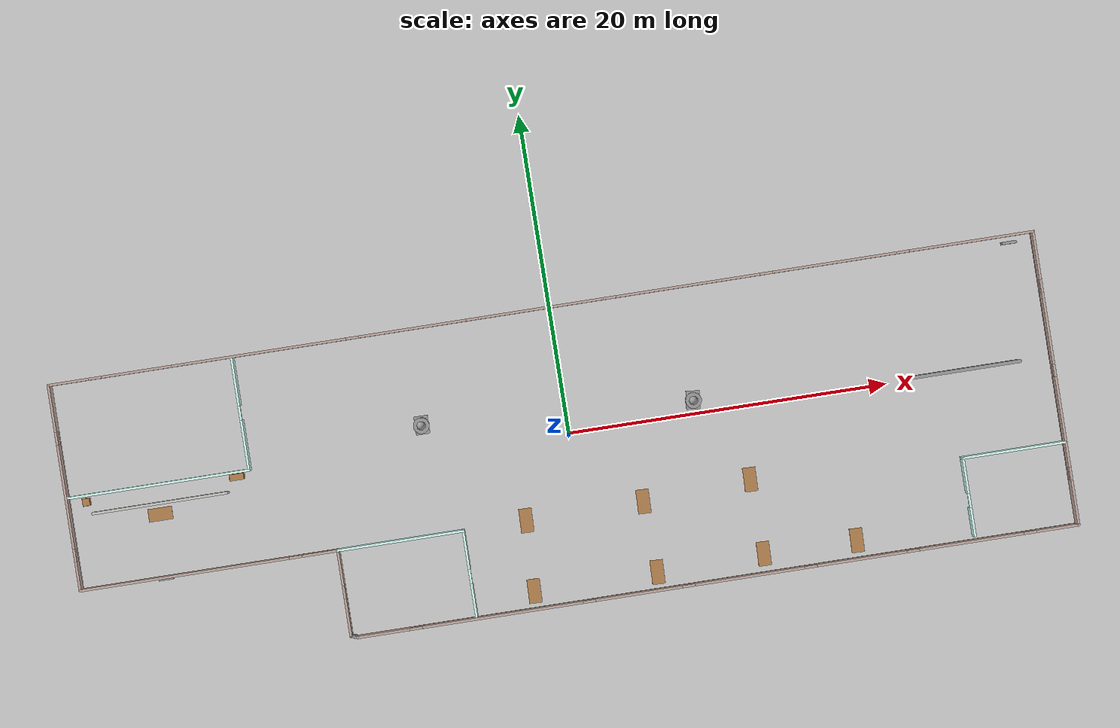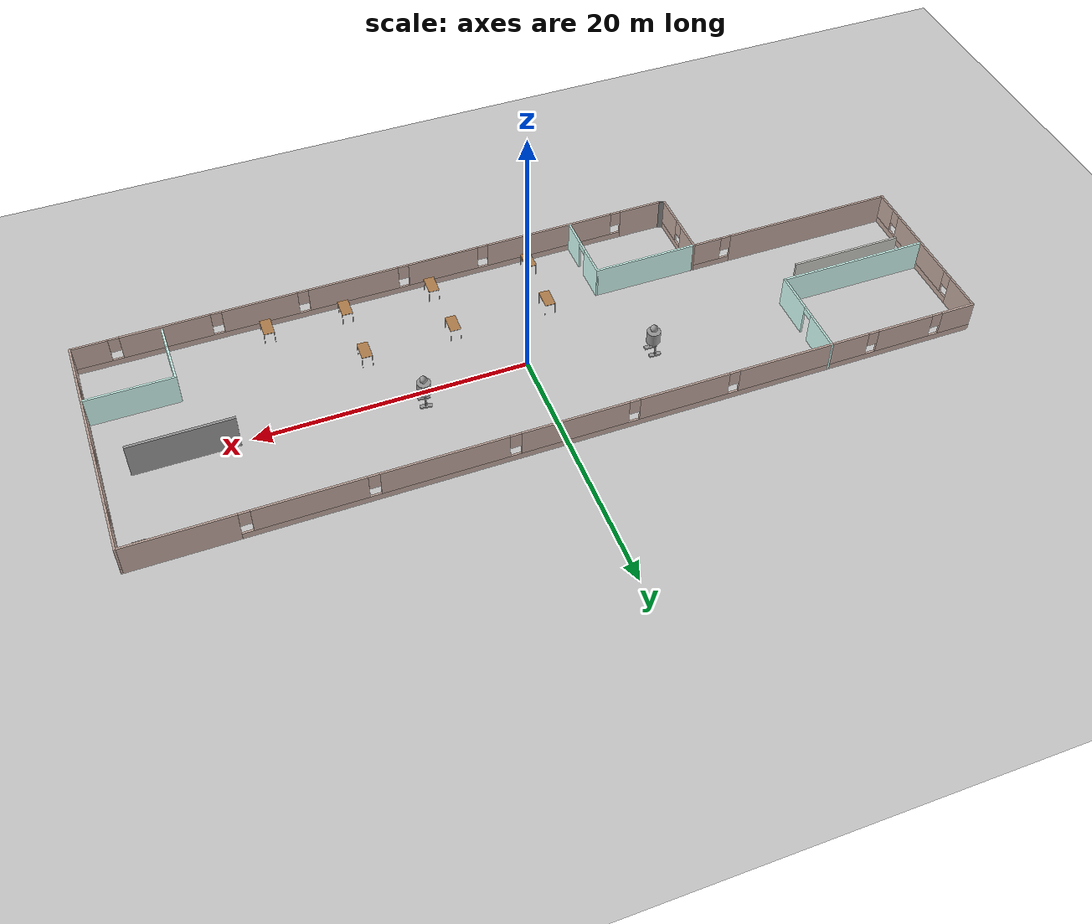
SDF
<sdf version="1.6">
 <world name="default">
  <plugin name="welcome" filename="libwelcome.so"/>
  <light name="sun" type="directional">
   <pose>0 0 10 0 -0 0</pose>
   <diffuse>0.8 0.8 0.8 1</diffuse>
   <specular>0.2 0.2 0.2 1</specular>
   <attenuation>
    <range>1000</range>
    <constant>0.9</constant>
    <linear>0.01</linear>
    <quadratic>0.001</quadratic>
   </attenuation>
   <direction>-0.5 0.1 -0.9</direction>
  </light>
  <model name="ground_plane">
   <static>1</static>
   <link name="link">
    <collision name="collision">
     <geometry><plane><normal>0 0 1</normal><size>100 100</size></plane></geometry>
     <surface>
      <contact><collide_bitmask>65535</collide_bitmask></contact>
      <friction><ode><mu>100</mu><mu2>50</mu2></ode></friction>
     </surface>
    </collision>
    <visual name="visual">
     <cast_shadows>0</cast_shadows>
     <geometry><plane><normal>0 0 1</normal><size>100 100</size></plane></geometry>
     <material>
      <script><uri>file://media/materials/scripts/gazebo.material</uri><name>Gazebo/Grey</name></script>
     </material>
    </visual>
   </link>
  </model>
  <gravity>0 0 -9.8</gravity>
  <magnetic_field>6e-06 2.3e-05 -4.2e-05</magnetic_field>
  <atmosphere type="adiabatic"/>
  <physics name="default_physics" default="0" type="ode">
   <max_step_size>0.001</max_step_size>
   <real_time_factor>1</real_time_factor>
   <real_time_update_rate>1000</real_time_update_rate>
  </physics>
  <scene><ambient>0.4 0.4 0.4 1</ambient><background>0.7 0.7 0.7 1</background><shadows>1</shadows></scene>
  <spherical_coordinates>
   <surface_model>EARTH_WGS84</surface_model>
   <latitude_deg>0</latitude_deg>
   <longitude_deg>0</longitude_deg>
   <elevation>0</elevation>
   <heading_deg>0</heading_deg>
  </spherical_coordinates>
  <model name="Building">
   <pose>-0.5104 -1.23056 0 0 -0 0</pose>
   <link name="Door_2">
    <collision name="Door_2_Collision">
     <geometry><box><size>0.9 0.17 2</size></box></geometry>
     <pose>0 0 1 0 -0 0</pose>
    </collision>
    <visual name="Door_2_Visual">
     <pose>0 0 1 0 -0 0</pose>
     <geometry><box><size>0.9 0.17 2</size></box></geometry>
     <material>
      <script><uri>file://media/materials/scripts/gazebo.material</uri><name>Gazebo/Grey</name></script>
     </material>
    </visual>
    <pose>-25.4725 -3.75552 0 0 -0 0</pose>
   </link>
   <link name="Door_3">
    <collision name="Door_3_Collision">
     <geometry><box><size>0.9 0.17 2</size></box></geometry>
     <pose>0 0 1 0 -0 0</pose>
    </collision>
    <visual name="Door_3_Visual">
     <pose>0 0 1 0 -0 0</pose>
     <geometry><box><size>0.9 0.17 2</size></box></geometry>
     <material>
      <script><uri>file://media/materials/scripts/gazebo.material</uri><name>Gazebo/Grey</name></script>
     </material>
    </visual>
    <pose>29.2873 8.73464 0 0 -0 0</pose>
   </link>
   <link name="Wall_21">
    <pose>8.25 -9.16807 0 0 -0 0</pose>
    <visual name="Wall_21_Visual_0">
     <pose>-20.9527 0 1.25 0 -0 0</pose>
     <geometry><box><size>3.34458 0.15 2.5</size></box></geometry>
     <material>
      <script><uri>file://media/materials/scripts/gazebo.material</uri><name>Gazebo/Grey</name></script>
      <ambient>0.760784 0.662745 0.627451 1</ambient>
     </material>
     <meta><layer>0</layer></meta>
    </visual>
    <collision name="Wall_21_Collision_0">
     <geometry><box><size>3.34458 0.15 2.5</size></box></geometry>
     <pose>-20.9527 0 1.25 0 -0 0</pose>
    </collision>
    <visual name="Wall_21_Visual_1">
     <pose>1.67229 0 0.25 0 -0 0</pose>
     <geometry><box><size>41.9054 0.15 0.5</size></box></geometry>
     <material>
      <script><uri>file://media/materials/scripts/gazebo.material</uri><name>Gazebo/Grey</name></script>
      <ambient>0.760784 0.662745 0.627451 1</ambient>
     </material>
     <meta><layer>0</layer></meta>
    </visual>
    <collision name="Wall_21_Collision_1">
     <geometry><box><size>41.9054 0.15 0.5</size></box></geometry>
     <pose>1.67229 0 0.25 0 -0 0</pose>
    </collision>
    <visual name="Wall_21_Visual_2">
     <pose>-13.466 0 1.5 0 -0 0</pose>
     <geometry><box><size>10.0289 0.15 2</size></box></geometry>
     <material>
      <script><uri>file://media/materials/scripts/gazebo.material</uri><name>Gazebo/Grey</name></script>
      <ambient>0.760784 0.662745 0.627451 1</ambient>
     </material>
     <meta><layer>0</layer></meta>
    </visual>
    <collision name="Wall_21_Collision_2">
     <geometry><box><size>10.0289 0.15 2</size></box></geometry>
     <pose>-13.466 0 1.5 0 -0 0</pose>
    </collision>
    <visual name="Wall_21_Visual_3">
     <pose>-4.94435 0 1.5 0 -0 0</pose>
     <geometry><box><size>5.41432 0.15 2</size></box></geometry>
     <material>
      <script><uri>file://media/materials/scripts/gazebo.material</uri><name>Gazebo/Grey</name></script>
      <ambient>0.760784 0.662745 0.627451 1</ambient>
     </material>
     <meta><layer>0</layer></meta>
    </visual>
    <collision name="Wall_21_Collision_3">
     <geometry><box><size>5.41432 0.15 2</size></box></geometry>
     <pose>-4.94435 0 1.5 0 -0 0</pose>
    </collision>
    <visual name="Wall_21_Visual_4">
     <pose>1.97753 0 1.5 0 -0 0</pose>
     <geometry><box><size>6.82946 0.15 2</size></box></geometry>
     <material>
      <script><uri>file://media/materials/scripts/gazebo.material</uri><name>Gazebo/Grey</name></script>
      <ambient>0.760784 0.662745 0.627451 1</ambient>
     </material>
     <meta><layer>0</layer></meta>
    </visual>
    <collision name="Wall_21_Collision_4">
     <geometry><box><size>6.82946 0.15 2</size></box></geometry>
     <pose>1.97753 0 1.5 0 -0 0</pose>
    </collision>
    <visual name="Wall_21_Visual_5">
     <pose>8.99171 0 1.5 0 -0 0</pose>
     <geometry><box><size>5.5989 0.15 2</size></box></geometry>
     <material>
      <script><uri>file://media/materials/scripts/gazebo.material</uri><name>Gazebo/Grey</name></script>
      <ambient>0.760784 0.662745 0.627451 1</ambient>
     </material>
     <meta><layer>0</layer></meta>
    </visual>
    <collision name="Wall_21_Collision_5">
     <geometry><box><size>5.5989 0.15 2</size></box></geometry>
     <pose>8.99171 0 1.5 0 -0 0</pose>
    </collision>
    <visual name="Wall_21_Visual_6">
     <pose>15.8521 0 1.5 0 -0 0</pose>
     <geometry><box><size>6.52182 0.15 2</size></box></geometry>
     <material>
      <script><uri>file://media/materials/scripts/gazebo.material</uri><name>Gazebo/Grey</name></script>
      <ambient>0.760784 0.662745 0.627451 1</ambient>
     </material>
     <meta><layer>0</layer></meta>
    </visual>
    <collision name="Wall_21_Collision_6">
     <geometry><box><size>6.52182 0.15 2</size></box></geometry>
     <pose>15.8521 0 1.5 0 -0 0</pose>
    </collision>
    <visual name="Wall_21_Visual_7">
     <pose>21.269 0 1.5 0 -0 0</pose>
     <geometry><box><size>2.71202 0.15 2</size></box></geometry>
     <material>
      <script><uri>file://media/materials/scripts/gazebo.material</uri><name>Gazebo/Grey</name></script>
      <ambient>0.760784 0.662745 0.627451 1</ambient>
     </material>
     <meta><layer>0</layer></meta>
    </visual>
    <collision name="Wall_21_Collision_7">
     <geometry><box><size>2.71202 0.15 2</size></box></geometry>
     <pose>21.269 0 1.5 0 -0 0</pose>
    </collision>
    <visual name="Wall_21_Visual_8">
     <pose>-18.8804 0 1.9 0 -0 0</pose>
     <geometry><box><size>0.8 0.15 1.2</size></box></geometry>
     <material>
      <script><uri>file://media/materials/scripts/gazebo.material</uri><name>Gazebo/Grey</name></script>
      <ambient>0.760784 0.662745 0.627451 1</ambient>
     </material>
     <meta><layer>0</layer></meta>
    </visual>
    <collision name="Wall_21_Collision_8">
     <geometry><box><size>0.8 0.15 1.2</size></box></geometry>
     <pose>-18.8804 0 1.9 0 -0 0</pose>
    </collision>
    <visual name="Wall_21_Visual_9">
     <pose>-8.05151 0 1.9 0 -0 0</pose>
     <geometry><box><size>0.8 0.15 1.2</size></box></geometry>
     <material>
      <script><uri>file://media/materials/scripts/gazebo.material</uri><name>Gazebo/Grey</name></script>
      <ambient>0.760784 0.662745 0.627451 1</ambient>
     </material>
     <meta><layer>0</layer></meta>
    </visual>
    <collision name="Wall_21_Collision_9">
     <geometry><box><size>0.8 0.15 1.2</size></box></geometry>
     <pose>-8.05151 0 1.9 0 -0 0</pose>
    </collision>
    <visual name="Wall_21_Visual_10">
     <pose>-1.83719 0 1.9 0 -0 0</pose>
     <geometry><box><size>0.8 0.15 1.2</size></box></geometry>
     <material>
      <script><uri>file://media/materials/scripts/gazebo.material</uri><name>Gazebo/Grey</name></script>
      <ambient>0.760784 0.662745 0.627451 1</ambient>
     </material>
     <meta><layer>0</layer></meta>
    </visual>
    <collision name="Wall_21_Collision_10">
     <geometry><box><size>0.8 0.15 1.2</size></box></geometry>
     <pose>-1.83719 0 1.9 0 -0 0</pose>
    </collision>
    <visual name="Wall_21_Visual_11">
     <pose>5.79226 0 1.9 0 -0 0</pose>
     <geometry><box><size>0.8 0.15 1.2</size></box></geometry>
     <material>
      <script><uri>file://media/materials/scripts/gazebo.material</uri><name>Gazebo/Grey</name></script>
      <ambient>0.760784 0.662745 0.627451 1</ambient>
     </material>
     <meta><layer>0</layer></meta>
    </visual>
    <collision name="Wall_21_Collision_11">
     <geometry><box><size>0.8 0.15 1.2</size></box></geometry>
     <pose>5.79226 0 1.9 0 -0 0</pose>
    </collision>
    <visual name="Wall_21_Visual_12">
     <pose>12.1912 0 1.9 0 -0 0</pose>
     <geometry><box><size>0.8 0.15 1.2</size></box></geometry>
     <material>
      <script><uri>file://media/materials/scripts/gazebo.material</uri><name>Gazebo/Grey</name></script>
      <ambient>0.760784 0.662745 0.627451 1</ambient>
     </material>
     <meta><layer>0</layer></meta>
    </visual>
    <collision name="Wall_21_Collision_12">
     <geometry><box><size>0.8 0.15 1.2</size></box></geometry>
     <pose>12.1912 0 1.9 0 -0 0</pose>
    </collision>
    <visual name="Wall_21_Visual_13">
     <pose>19.513 0 1.9 0 -0 0</pose>
     <geometry><box><size>0.8 0.15 1.2</size></box></geometry>
     <material>
      <script><uri>file://media/materials/scripts/gazebo.material</uri><name>Gazebo/Grey</name></script>
      <ambient>0.760784 0.662745 0.627451 1</ambient>
     </material>
     <meta><layer>0</layer></meta>
    </visual>
    <collision name="Wall_21_Collision_13">
     <geometry><box><size>0.8 0.15 1.2</size></box></geometry>
     <pose>19.513 0 1.9 0 -0 0</pose>
    </collision>
   </link>
   <link name="Wall_22">
    <pose>30.8 0.006928 0 0 -0 1.5708</pose>
    <visual name="Wall_22_Visual_0">
     <pose>-7.8084 0 1.25 0 -0 0</pose>
     <geometry><box><size>2.88319 0.15 2.5</size></box></geometry>
     <material>
      <script><uri>file://media/materials/scripts/gazebo.material</uri><name>Gazebo/Grey</name></script>
      <ambient>0.760784 0.662745 0.627451 1</ambient>
     </material>
     <meta><layer>0</layer></meta>
    </visual>
    <collision name="Wall_22_Collision_0">
     <geometry><box><size>2.88319 0.15 2.5</size></box></geometry>
     <pose>-7.8084 0 1.25 0 -0 0</pose>
    </collision>
    <visual name="Wall_22_Visual_1">
     <pose>1.44159 0 0.25 0 -0 0</pose>
     <geometry><box><size>15.6168 0.15 0.5</size></box></geometry>
     <material>
      <script><uri>file://media/materials/scripts/gazebo.material</uri><name>Gazebo/Grey</name></script>
      <ambient>0.760784 0.662745 0.627451 1</ambient>
     </material>
     <meta><layer>0</layer></meta>
    </visual>
    <collision name="Wall_22_Collision_1">
     <geometry><box><size>15.6168 0.15 0.5</size></box></geometry>
     <pose>1.44159 0 0.25 0 -0 0</pose>
    </collision>
    <visual name="Wall_22_Visual_2">
     <pose>-2.7366 0 1.5 0 -0 0</pose>
     <geometry><box><size>5.66043 0.15 2</size></box></geometry>
     <material>
      <script><uri>file://media/materials/scripts/gazebo.material</uri><name>Gazebo/Grey</name></script>
      <ambient>0.760784 0.662745 0.627451 1</ambient>
     </material>
     <meta><layer>0</layer></meta>
    </visual>
    <collision name="Wall_22_Collision_2">
     <geometry><box><size>5.66043 0.15 2</size></box></geometry>
     <pose>-2.7366 0 1.5 0 -0 0</pose>
    </collision>
    <visual name="Wall_22_Visual_3">
     <pose>3.13931 0 1.5 0 -0 0</pose>
     <geometry><box><size>4.4914 0.15 2</size></box></geometry>
     <material>
      <script><uri>file://media/materials/scripts/gazebo.material</uri><name>Gazebo/Grey</name></script>
      <ambient>0.760784 0.662745 0.627451 1</ambient>
     </material>
     <meta><layer>0</layer></meta>
    </visual>
    <collision name="Wall_22_Collision_3">
     <geometry><box><size>4.4914 0.15 2</size></box></geometry>
     <pose>3.13931 0 1.5 0 -0 0</pose>
    </collision>
    <visual name="Wall_22_Visual_4">
     <pose>7.71751 0 1.5 0 -0 0</pose>
     <geometry><box><size>3.06499 0.15 2</size></box></geometry>
     <material>
      <script><uri>file://media/materials/scripts/gazebo.material</uri><name>Gazebo/Grey</name></script>
      <ambient>0.760784 0.662745 0.627451 1</ambient>
     </material>
     <meta><layer>0</layer></meta>
    </visual>
    <collision name="Wall_22_Collision_4">
     <geometry><box><size>3.06499 0.15 2</size></box></geometry>
     <pose>7.71751 0 1.5 0 -0 0</pose>
    </collision>
    <visual name="Wall_22_Visual_5">
     <pose>-5.96681 0 1.9 0 -0 0</pose>
     <geometry><box><size>0.8 0.15 1.2</size></box></geometry>
     <material>
      <script><uri>file://media/materials/scripts/gazebo.material</uri><name>Gazebo/Grey</name></script>
      <ambient>0.760784 0.662745 0.627451 1</ambient>
     </material>
     <meta><layer>0</layer></meta>
    </visual>
    <collision name="Wall_22_Collision_5">
     <geometry><box><size>0.8 0.15 1.2</size></box></geometry>
     <pose>-5.96681 0 1.9 0 -0 0</pose>
    </collision>
    <visual name="Wall_22_Visual_6">
     <pose>0.493616 0 1.9 0 -0 0</pose>
     <geometry><box><size>0.8 0.15 1.2</size></box></geometry>
     <material>
      <script><uri>file://media/materials/scripts/gazebo.material</uri><name>Gazebo/Grey</name></script>
      <ambient>0.760784 0.662745 0.627451 1</ambient>
     </material>
     <meta><layer>0</layer></meta>
    </visual>
    <collision name="Wall_22_Collision_6">
     <geometry><box><size>0.8 0.15 1.2</size></box></geometry>
     <pose>0.493616 0 1.9 0 -0 0</pose>
    </collision>
    <visual name="Wall_22_Visual_7">
     <pose>5.78501 0 1.9 0 -0 0</pose>
     <geometry><box><size>0.8 0.15 1.2</size></box></geometry>
     <material>
      <script><uri>file://media/materials/scripts/gazebo.material</uri><name>Gazebo/Grey</name></script>
      <ambient>0.760784 0.662745 0.627451 1</ambient>
     </material>
     <meta><layer>0</layer></meta>
    </visual>
    <collision name="Wall_22_Collision_7">
     <geometry><box><size>0.8 0.15 1.2</size></box></geometry>
     <pose>5.78501 0 1.9 0 -0 0</pose>
    </collision>
   </link>
   <link name="Wall_23">
    <pose>0 9.18193 0 0 -0 3.14159</pose>
    <visual name="Wall_23_Visual_0">
     <pose>-26.9656 0 1.25 0 -0 0</pose>
     <geometry><box><size>7.81883 0.15 2.5</size></box></geometry>
     <material>
      <script><uri>file://media/materials/scripts/gazebo.material</uri><name>Gazebo/Grey</name></script>
      <ambient>0.760784 0.662745 0.627451 1</ambient>
     </material>
     <meta><layer>0</layer></meta>
    </visual>
    <collision name="Wall_23_Collision_0">
     <geometry><box><size>7.81883 0.15 2.5</size></box></geometry>
     <pose>-26.9656 0 1.25 0 -0 0</pose>
    </collision>
    <visual name="Wall_23_Visual_1">
     <pose>3.90942 0 0.25 0 -0 0</pose>
     <geometry><box><size>53.9312 0.15 0.5</size></box></geometry>
     <material>
      <script><uri>file://media/materials/scripts/gazebo.material</uri><name>Gazebo/Grey</name></script>
      <ambient>0.760784 0.662745 0.627451 1</ambient>
     </material>
     <meta><layer>0</layer></meta>
    </visual>
    <collision name="Wall_23_Collision_1">
     <geometry><box><size>53.9312 0.15 0.5</size></box></geometry>
     <pose>3.90942 0 0.25 0 -0 0</pose>
    </collision>
    <visual name="Wall_23_Visual_2">
     <pose>-18.38 0 1.5 0 -0 0</pose>
     <geometry><box><size>7.75237 0.15 2</size></box></geometry>
     <material>
      <script><uri>file://media/materials/scripts/gazebo.material</uri><name>Gazebo/Grey</name></script>
      <ambient>0.760784 0.662745 0.627451 1</ambient>
     </material>
     <meta><layer>0</layer></meta>
    </visual>
    <collision name="Wall_23_Collision_2">
     <geometry><box><size>7.75237 0.15 2</size></box></geometry>
     <pose>-18.38 0 1.5 0 -0 0</pose>
    </collision>
    <visual name="Wall_23_Visual_3">
     <pose>-9.21232 0 1.5 0 -0 0</pose>
     <geometry><box><size>8.98293 0.15 2</size></box></geometry>
     <material>
      <script><uri>file://media/materials/scripts/gazebo.material</uri><name>Gazebo/Grey</name></script>
      <ambient>0.760784 0.662745 0.627451 1</ambient>
     </material>
     <meta><layer>0</layer></meta>
    </visual>
    <collision name="Wall_23_Collision_3">
     <geometry><box><size>8.98293 0.15 2</size></box></geometry>
     <pose>-9.21232 0 1.5 0 -0 0</pose>
    </collision>
    <visual name="Wall_23_Visual_4">
     <pose>-0.013907 0 1.5 0 -0 0</pose>
     <geometry><box><size>7.8139 0.15 2</size></box></geometry>
     <material>
      <script><uri>file://media/materials/scripts/gazebo.material</uri><name>Gazebo/Grey</name></script>
      <ambient>0.760784 0.662745 0.627451 1</ambient>
     </material>
     <meta><layer>0</layer></meta>
    </visual>
    <collision name="Wall_23_Collision_4">
     <geometry><box><size>7.8139 0.15 2</size></box></geometry>
     <pose>-0.013907 0 1.5 0 -0 0</pose>
    </collision>
    <visual name="Wall_23_Visual_5">
     <pose>8.04625 0 1.5 0 -0 0</pose>
     <geometry><box><size>6.7064 0.15 2</size></box></geometry>
     <material>
      <script><uri>file://media/materials/scripts/gazebo.material</uri><name>Gazebo/Grey</name></script>
      <ambient>0.760784 0.662745 0.627451 1</ambient>
     </material>
     <meta><layer>0</layer></meta>
    </visual>
    <collision name="Wall_23_Collision_5">
     <geometry><box><size>6.7064 0.15 2</size></box></geometry>
     <pose>8.04625 0 1.5 0 -0 0</pose>
    </collision>
    <visual name="Wall_23_Visual_6">
     <pose>17.2447 0 1.5 0 -0 0</pose>
     <geometry><box><size>10.0904 0.15 2</size></box></geometry>
     <material>
      <script><uri>file://media/materials/scripts/gazebo.material</uri><name>Gazebo/Grey</name></script>
      <ambient>0.760784 0.662745 0.627451 1</ambient>
     </material>
     <meta><layer>0</layer></meta>
    </visual>
    <collision name="Wall_23_Collision_6">
     <geometry><box><size>10.0904 0.15 2</size></box></geometry>
     <pose>17.2447 0 1.5 0 -0 0</pose>
    </collision>
    <visual name="Wall_23_Visual_7">
     <pose>25.2741 0 1.5 0 -0 0</pose>
     <geometry><box><size>4.36834 0.15 2</size></box></geometry>
     <material>
      <script><uri>file://media/materials/scripts/gazebo.material</uri><name>Gazebo/Grey</name></script>
      <ambient>0.760784 0.662745 0.627451 1</ambient>
     </material>
     <meta><layer>0</layer></meta>
    </visual>
    <collision name="Wall_23_Collision_7">
     <geometry><box><size>4.36834 0.15 2</size></box></geometry>
     <pose>25.2741 0 1.5 0 -0 0</pose>
    </collision>
    <visual name="Wall_23_Visual_8">
     <pose>29.5666 0 1.5 0 -0 0</pose>
     <geometry><box><size>2.61678 0.15 2</size></box></geometry>
     <material>
      <script><uri>file://media/materials/scripts/gazebo.material</uri><name>Gazebo/Grey</name></script>
      <ambient>0.760784 0.662745 0.627451 1</ambient>
     </material>
     <meta><layer>0</layer></meta>
    </visual>
    <collision name="Wall_23_Collision_8">
     <geometry><box><size>2.61678 0.15 2</size></box></geometry>
     <pose>29.5666 0 1.5 0 -0 0</pose>
    </collision>
    <visual name="Wall_23_Visual_9">
     <pose>-22.6562 0 1.9 0 -0 0</pose>
     <geometry><box><size>0.8 0.15 1.2</size></box></geometry>
     <material>
      <script><uri>file://media/materials/scripts/gazebo.material</uri><name>Gazebo/Grey</name></script>
      <ambient>0.760784 0.662745 0.627451 1</ambient>
     </material>
     <meta><layer>0</layer></meta>
    </visual>
    <collision name="Wall_23_Collision_9">
     <geometry><box><size>0.8 0.15 1.2</size></box></geometry>
     <pose>-22.6562 0 1.9 0 -0 0</pose>
    </collision>
    <visual name="Wall_23_Visual_10">
     <pose>-14.1038 0 1.9 0 -0 0</pose>
     <geometry><box><size>0.8 0.15 1.2</size></box></geometry>
     <material>
      <script><uri>file://media/materials/scripts/gazebo.material</uri><name>Gazebo/Grey</name></script>
      <ambient>0.760784 0.662745 0.627451 1</ambient>
     </material>
     <meta><layer>0</layer></meta>
    </visual>
    <collision name="Wall_23_Collision_10">
     <geometry><box><size>0.8 0.15 1.2</size></box></geometry>
     <pose>-14.1038 0 1.9 0 -0 0</pose>
    </collision>
    <visual name="Wall_23_Visual_11">
     <pose>-4.32086 0 1.9 0 -0 0</pose>
     <geometry><box><size>0.8 0.15 1.2</size></box></geometry>
     <material>
      <script><uri>file://media/materials/scripts/gazebo.material</uri><name>Gazebo/Grey</name></script>
      <ambient>0.760784 0.662745 0.627451 1</ambient>
     </material>
     <meta><layer>0</layer></meta>
    </visual>
    <collision name="Wall_23_Collision_11">
     <geometry><box><size>0.8 0.15 1.2</size></box></geometry>
     <pose>-4.32086 0 1.9 0 -0 0</pose>
    </collision>
    <visual name="Wall_23_Visual_12">
     <pose>4.29304 0 1.9 0 -0 0</pose>
     <geometry><box><size>0.8 0.15 1.2</size></box></geometry>
     <material>
      <script><uri>file://media/materials/scripts/gazebo.material</uri><name>Gazebo/Grey</name></script>
      <ambient>0.760784 0.662745 0.627451 1</ambient>
     </material>
     <meta><layer>0</layer></meta>
    </visual>
    <collision name="Wall_23_Collision_12">
     <geometry><box><size>0.8 0.15 1.2</size></box></geometry>
     <pose>4.29304 0 1.9 0 -0 0</pose>
    </collision>
    <visual name="Wall_23_Visual_13">
     <pose>11.7994 0 1.9 0 -0 0</pose>
     <geometry><box><size>0.8 0.15 1.2</size></box></geometry>
     <material>
      <script><uri>file://media/materials/scripts/gazebo.material</uri><name>Gazebo/Grey</name></script>
      <ambient>0.760784 0.662745 0.627451 1</ambient>
     </material>
     <meta><layer>0</layer></meta>
    </visual>
    <collision name="Wall_23_Collision_13">
     <geometry><box><size>0.8 0.15 1.2</size></box></geometry>
     <pose>11.7994 0 1.9 0 -0 0</pose>
    </collision>
    <visual name="Wall_23_Visual_14">
     <pose>22.6899 0 1.9 0 -0 0</pose>
     <geometry><box><size>0.8 0.15 1.2</size></box></geometry>
     <material>
      <script><uri>file://media/materials/scripts/gazebo.material</uri><name>Gazebo/Grey</name></script>
      <ambient>0.760784 0.662745 0.627451 1</ambient>
     </material>
     <meta><layer>0</layer></meta>
    </visual>
    <collision name="Wall_23_Collision_14">
     <geometry><box><size>0.8 0.15 1.2</size></box></geometry>
     <pose>22.6899 0 1.9 0 -0 0</pose>
    </collision>
    <visual name="Wall_23_Visual_15">
     <pose>27.8582 0 1.9 0 -0 0</pose>
     <geometry><box><size>0.8 0.15 1.2</size></box></geometry>
     <material>
      <script><uri>file://media/materials/scripts/gazebo.material</uri><name>Gazebo/Grey</name></script>
      <ambient>0.760784 0.662745 0.627451 1</ambient>
     </material>
     <meta><layer>0</layer></meta>
    </visual>
    <collision name="Wall_23_Collision_15">
     <geometry><box><size>0.8 0.15 1.2</size></box></geometry>
     <pose>27.8582 0 1.9 0 -0 0</pose>
    </collision>
   </link>
   <link name="Wall_24">
    <pose>-30.8 2.75693 0 0 0 -1.5708</pose>
    <visual name="Wall_24_Visual_0">
     <pose>-4.99827 0 1.25 0 -0 0</pose>
     <geometry><box><size>3.00346 0.15 2.5</size></box></geometry>
     <material>
      <script><uri>file://media/materials/scripts/gazebo.material</uri><name>Gazebo/Grey</name></script>
      <ambient>0.760784 0.662745 0.627451 1</ambient>
     </material>
     <meta><layer>0</layer></meta>
    </visual>
    <collision name="Wall_24_Collision_0">
     <geometry><box><size>3.00346 0.15 2.5</size></box></geometry>
     <pose>-4.99827 0 1.25 0 -0 0</pose>
    </collision>
    <visual name="Wall_24_Visual_1">
     <pose>1.50173 0 0.25 0 -0 0</pose>
     <geometry><box><size>9.99654 0.15 0.5</size></box></geometry>
     <material>
      <script><uri>file://media/materials/scripts/gazebo.material</uri><name>Gazebo/Grey</name></script>
      <ambient>0.760784 0.662745 0.627451 1</ambient>
     </material>
     <meta><layer>0</layer></meta>
    </visual>
    <collision name="Wall_24_Collision_1">
     <geometry><box><size>9.99654 0.15 0.5</size></box></geometry>
     <pose>1.50173 0 0.25 0 -0 0</pose>
    </collision>
    <visual name="Wall_24_Visual_2">
     <pose>0.564367 0 1.5 0 -0 0</pose>
     <geometry><box><size>6.52182 0.15 2</size></box></geometry>
     <material>
      <script><uri>file://media/materials/scripts/gazebo.material</uri><name>Gazebo/Grey</name></script>
      <ambient>0.760784 0.662745 0.627451 1</ambient>
     </material>
     <meta><layer>0</layer></meta>
    </visual>
    <collision name="Wall_24_Collision_2">
     <geometry><box><size>6.52182 0.15 2</size></box></geometry>
     <pose>0.564367 0 1.5 0 -0 0</pose>
    </collision>
    <visual name="Wall_24_Visual_3">
     <pose>5.56264 0 1.5 0 -0 0</pose>
     <geometry><box><size>1.87472 0.15 2</size></box></geometry>
     <material>
      <script><uri>file://media/materials/scripts/gazebo.material</uri><name>Gazebo/Grey</name></script>
      <ambient>0.760784 0.662745 0.627451 1</ambient>
     </material>
     <meta><layer>0</layer></meta>
    </visual>
    <collision name="Wall_24_Collision_3">
     <geometry><box><size>1.87472 0.15 2</size></box></geometry>
     <pose>5.56264 0 1.5 0 -0 0</pose>
    </collision>
    <visual name="Wall_24_Visual_4">
     <pose>-3.09654 0 1.9 0 -0 0</pose>
     <geometry><box><size>0.8 0.15 1.2</size></box></geometry>
     <material>
      <script><uri>file://media/materials/scripts/gazebo.material</uri><name>Gazebo/Grey</name></script>
      <ambient>0.760784 0.662745 0.627451 1</ambient>
     </material>
     <meta><layer>0</layer></meta>
    </visual>
    <collision name="Wall_24_Collision_4">
     <geometry><box><size>0.8 0.15 1.2</size></box></geometry>
     <pose>-3.09654 0 1.9 0 -0 0</pose>
    </collision>
    <visual name="Wall_24_Visual_5">
     <pose>4.22528 0 1.9 0 -0 0</pose>
     <geometry><box><size>0.8 0.15 1.2</size></box></geometry>
     <material>
      <script><uri>file://media/materials/scripts/gazebo.material</uri><name>Gazebo/Grey</name></script>
      <ambient>0.760784 0.662745 0.627451 1</ambient>
     </material>
     <meta><layer>0</layer></meta>
    </visual>
    <collision name="Wall_24_Collision_5">
     <geometry><box><size>0.8 0.15 1.2</size></box></geometry>
     <pose>4.22528 0 1.9 0 -0 0</pose>
    </collision>
   </link>
   <link name="Wall_25">
    <pose>-22.75 -3.66807 0 0 -0 0</pose>
    <visual name="Wall_25_Visual_0">
     <pose>-1.55598 0 1.25 0 -0 0</pose>
     <geometry><box><size>13.138 0.15 2.5</size></box></geometry>
     <material>
      <script><uri>file://media/materials/scripts/gazebo.material</uri><name>Gazebo/Grey</name></script>
      <ambient>0.760784 0.662745 0.627451 1</ambient>
     </material>
     <meta><layer>0</layer></meta>
    </visual>
    <collision name="Wall_25_Collision_0">
     <geometry><box><size>13.138 0.15 2.5</size></box></geometry>
     <pose>-1.55598 0 1.25 0 -0 0</pose>
    </collision>
    <visual name="Wall_25_Visual_1">
     <pose>6.56902 0 0.25 0 -0 0</pose>
     <geometry><box><size>3.11195 0.15 0.5</size></box></geometry>
     <material>
      <script><uri>file://media/materials/scripts/gazebo.material</uri><name>Gazebo/Grey</name></script>
      <ambient>0.760784 0.662745 0.627451 1</ambient>
     </material>
     <meta><layer>0</layer></meta>
    </visual>
    <collision name="Wall_25_Collision_1">
     <geometry><box><size>3.11195 0.15 0.5</size></box></geometry>
     <pose>6.56902 0 0.25 0 -0 0</pose>
    </collision>
    <visual name="Wall_25_Visual_2">
     <pose>6.96902 0 1.5 0 -0 0</pose>
     <geometry><box><size>2.31195 0.15 2</size></box></geometry>
     <material>
      <script><uri>file://media/materials/scripts/gazebo.material</uri><name>Gazebo/Grey</name></script>
      <ambient>0.760784 0.662745 0.627451 1</ambient>
     </material>
     <meta><layer>0</layer></meta>
    </visual>
    <collision name="Wall_25_Collision_2">
     <geometry><box><size>2.31195 0.15 2</size></box></geometry>
     <pose>6.96902 0 1.5 0 -0 0</pose>
    </collision>
    <visual name="Wall_25_Visual_3">
     <pose>5.41305 0 1.9 0 -0 0</pose>
     <geometry><box><size>0.8 0.15 1.2</size></box></geometry>
     <material>
      <script><uri>file://media/materials/scripts/gazebo.material</uri><name>Gazebo/Grey</name></script>
      <ambient>0.760784 0.662745 0.627451 1</ambient>
     </material>
     <meta><layer>0</layer></meta>
    </visual>
    <collision name="Wall_25_Collision_3">
     <geometry><box><size>0.8 0.15 1.2</size></box></geometry>
     <pose>5.41305 0 1.9 0 -0 0</pose>
    </collision>
   </link>
   <link name="Wall_26">
    <pose>-14.7 -6.34307 0 0 0 -1.5708</pose>
    <visual name="Wall_26_Visual_0">
     <pose>-1.61278 0 1.25 0 -0 0</pose>
     <geometry><box><size>2.27445 0.15 2.5</size></box></geometry>
     <material>
      <script><uri>file://media/materials/scripts/gazebo.material</uri><name>Gazebo/Grey</name></script>
      <ambient>0.760784 0.662745 0.627451 1</ambient>
     </material>
     <meta><layer>0</layer></meta>
    </visual>
    <collision name="Wall_26_Collision_0">
     <geometry><box><size>2.27445 0.15 2.5</size></box></geometry>
     <pose>-1.61278 0 1.25 0 -0 0</pose>
    </collision>
    <visual name="Wall_26_Visual_1">
     <pose>1.13722 0 0.25 0 -0 0</pose>
     <geometry><box><size>3.22555 0.15 0.5</size></box></geometry>
     <material>
      <script><uri>file://media/materials/scripts/gazebo.material</uri><name>Gazebo/Grey</name></script>
      <ambient>0.760784 0.662745 0.627451 1</ambient>
     </material>
     <meta><layer>0</layer></meta>
    </visual>
    <collision name="Wall_26_Collision_1">
     <geometry><box><size>3.22555 0.15 0.5</size></box></geometry>
     <pose>1.13722 0 0.25 0 -0 0</pose>
    </collision>
    <visual name="Wall_26_Visual_2">
     <pose>1.53723 0 1.5 0 -0 0</pose>
     <geometry><box><size>2.42555 0.15 2</size></box></geometry>
     <material>
      <script><uri>file://media/materials/scripts/gazebo.material</uri><name>Gazebo/Grey</name></script>
      <ambient>0.760784 0.662745 0.627451 1</ambient>
     </material>
     <meta><layer>0</layer></meta>
    </visual>
    <collision name="Wall_26_Collision_2">
     <geometry><box><size>2.42555 0.15 2</size></box></geometry>
     <pose>1.53723 0 1.5 0 -0 0</pose>
    </collision>
    <visual name="Wall_26_Visual_3">
     <pose>-0.07555 0 1.9 0 -0 0</pose>
     <geometry><box><size>0.8 0.15 1.2</size></box></geometry>
     <material>
      <script><uri>file://media/materials/scripts/gazebo.material</uri><name>Gazebo/Grey</name></script>
      <ambient>0.760784 0.662745 0.627451 1</ambient>
     </material>
     <meta><layer>0</layer></meta>
    </visual>
    <collision name="Wall_26_Collision_3">
     <geometry><box><size>0.8 0.15 1.2</size></box></geometry>
     <pose>-0.07555 0 1.9 0 -0 0</pose>
    </collision>
   </link>
   <link name="Wall_27">
    <collision name="Wall_27_Collision">
     <geometry><box><size>0.5772 0.15 2.5</size></box></geometry>
     <pose>0 0 1.25 0 -0 0</pose>
    </collision>
    <visual name="Wall_27_Visual">
     <pose>0 0 1.25 0 -0 0</pose>
     <geometry><box><size>0.5772 0.15 2.5</size></box></geometry>
     <material>
      <script><uri>file://media/materials/scripts/gazebo.material</uri><name>Gazebo/Grey</name></script>
      <ambient>1 1 1 1</ambient>
     </material>
     <meta><layer>0</layer></meta>
    </visual>
    <pose>-14.5 -9.09307 0 0 0 -0.358771</pose>
   </link>
   <link name="Wall_31">
    <pose>-19.3563 5.63963 0 0 -0 1.5708</pose>
    <visual name="Wall_31_Visual_0">
     <pose>-2.02287 0 1.25 0 -0 0</pose>
     <geometry><box><size>3.20426 0.15 2.5</size></box></geometry>
     <material>
      <script><uri>file://media/materials/scripts/gazebo.material</uri><name>Gazebo/Grey</name></script>
      <ambient>0.831373 1 0.964706 1</ambient>
     </material>
     <meta><layer>0</layer></meta>
    </visual>
    <collision name="Wall_31_Collision_0">
     <geometry><box><size>3.20426 0.15 2.5</size></box></geometry>
     <pose>-2.02287 0 1.25 0 -0 0</pose>
    </collision>
    <visual name="Wall_31_Visual_1">
     <pose>2.05213 0 1.25 0 -0 0</pose>
     <geometry><box><size>3.14574 0.15 2.5</size></box></geometry>
     <material>
      <script><uri>file://media/materials/scripts/gazebo.material</uri><name>Gazebo/Grey</name></script>
      <ambient>0.831373 1 0.964706 1</ambient>
     </material>
     <meta><layer>0</layer></meta>
    </visual>
    <collision name="Wall_31_Collision_1">
     <geometry><box><size>3.14574 0.15 2.5</size></box></geometry>
     <pose>2.05213 0 1.25 0 -0 0</pose>
    </collision>
    <visual name="Wall_31_Visual_2">
     <pose>0.029256 0 2.25 0 -0 0</pose>
     <geometry><box><size>0.9 0.15 0.5</size></box></geometry>
     <material>
      <script><uri>file://media/materials/scripts/gazebo.material</uri><name>Gazebo/Grey</name></script>
      <ambient>0.831373 1 0.964706 1</ambient>
     </material>
     <meta><layer>0</layer></meta>
    </visual>
    <collision name="Wall_31_Collision_2">
     <geometry><box><size>0.9 0.15 0.5</size></box></geometry>
     <pose>0.029256 0 2.25 0 -0 0</pose>
    </collision>
   </link>
   <link name="Wall_33">
    <collision name="Wall_33_Collision">
     <geometry><box><size>11.5 0.15 2.5</size></box></geometry>
     <pose>0 0 1.25 0 -0 0</pose>
    </collision>
    <visual name="Wall_33_Visual">
     <pose>0 0 1.25 0 -0 0</pose>
     <geometry><box><size>11.5 0.15 2.5</size></box></geometry>
     <material>
      <script><uri>file://media/materials/scripts/gazebo.material</uri><name>Gazebo/Grey</name></script>
      <ambient>0.831373 1 0.964706 1</ambient>
     </material>
     <meta><layer>0</layer></meta>
    </visual>
    <pose>-25.0313 2.08963 0 0 -0 3.14159</pose>
   </link>
   <link name="Wall_35">
    <collision name="Wall_35_Collision">
     <geometry><box><size>8.5 0.15 2.5</size></box></geometry>
     <pose>0 0 1.25 0 -0 0</pose>
    </collision>
    <visual name="Wall_35_Visual">
     <pose>0 0 1.25 0 -0 0</pose>
     <geometry><box><size>8.5 0.15 2.5</size></box></geometry>
     <material>
      <script><uri>file://media/materials/scripts/gazebo.material</uri><name>Gazebo/CeilingTiled</name></script>
      <ambient>1 1 1 1</ambient>
     </material>
     <meta><layer>0</layer></meta>
    </visual>
    <pose>-25.1122 0.9206 0 0 -0 0</pose>
   </link>
   <link name="Wall_37">
    <collision name="Wall_37_Collision">
     <geometry><box><size>6.5 0.15 2.5</size></box></geometry>
     <pose>0 0 1.25 0 -0 0</pose>
    </collision>
    <visual name="Wall_37_Visual">
     <pose>0 0 1.25 0 -0 0</pose>
     <geometry><box><size>6.5 0.15 2.5</size></box></geometry>
     <material>
      <script><uri>file://media/materials/scripts/gazebo.material</uri><name>Gazebo/Grey</name></script>
      <ambient>0.831373 1 0.964706 1</ambient>
     </material>
     <meta><layer>0</layer></meta>
    </visual>
    <pose>27.5413 -3.99099 0 0 -0 3.14159</pose>
   </link>
   <link name="Wall_38">
    <pose>24.3663 -6.41599 0 0 0 -1.5708</pose>
    <visual name="Wall_38_Visual_0">
     <pose>-1.36465 0 1.25 0 -0 0</pose>
     <geometry><box><size>2.2707 0.15 2.5</size></box></geometry>
     <material>
      <script><uri>file://media/materials/scripts/gazebo.material</uri><name>Gazebo/Grey</name></script>
      <ambient>0.831373 1 0.964706 1</ambient>
     </material>
     <meta><layer>0</layer></meta>
    </visual>
    <collision name="Wall_38_Collision_0">
     <geometry><box><size>2.2707 0.15 2.5</size></box></geometry>
     <pose>-1.36465 0 1.25 0 -0 0</pose>
    </collision>
    <visual name="Wall_38_Visual_1">
     <pose>1.58535 0 1.25 0 -0 0</pose>
     <geometry><box><size>1.8293 0.15 2.5</size></box></geometry>
     <material>
      <script><uri>file://media/materials/scripts/gazebo.material</uri><name>Gazebo/Grey</name></script>
      <ambient>0.831373 1 0.964706 1</ambient>
     </material>
     <meta><layer>0</layer></meta>
    </visual>
    <collision name="Wall_38_Collision_1">
     <geometry><box><size>1.8293 0.15 2.5</size></box></geometry>
     <pose>1.58535 0 1.25 0 -0 0</pose>
    </collision>
    <visual name="Wall_38_Visual_2">
     <pose>0.220698 0 2.25 0 -0 0</pose>
     <geometry><box><size>0.9 0.15 0.5</size></box></geometry>
     <material>
      <script><uri>file://media/materials/scripts/gazebo.material</uri><name>Gazebo/Grey</name></script>
      <ambient>0.831373 1 0.964706 1</ambient>
     </material>
     <meta><layer>0</layer></meta>
    </visual>
    <collision name="Wall_38_Collision_2">
     <geometry><box><size>0.9 0.15 0.5</size></box></geometry>
     <pose>0.220698 0 2.25 0 -0 0</pose>
    </collision>
   </link>
   <link name="Wall_40">
    <collision name="Wall_40_Collision">
     <geometry><box><size>8 0.15 2.5</size></box></geometry>
     <pose>0 0 1.25 0 -0 0</pose>
    </collision>
    <visual name="Wall_40_Visual">
     <pose>0 0 1.25 0 -0 0</pose>
     <geometry><box><size>8 0.15 2.5</size></box></geometry>
     <material>
      <script><uri>file://media/materials/scripts/gazebo.material</uri><name>Gazebo/Grey</name></script>
      <ambient>0.831373 1 0.964706 1</ambient>
     </material>
     <meta><layer>0</layer></meta>
    </visual>
    <pose>-10.775 -3.66807 0 0 -0 0</pose>
   </link>
   <link name="Wall_41">
    <pose>-6.85 -6.34307 0 0 0 -1.5708</pose>
    <visual name="Wall_41_Visual_0">
     <pose>-1.51472 0 1.25 0 -0 0</pose>
     <geometry><box><size>2.47056 0.15 2.5</size></box></geometry>
     <material>
      <script><uri>file://media/materials/scripts/gazebo.material</uri><name>Gazebo/Grey</name></script>
      <ambient>0.831373 1 0.964706 1</ambient>
     </material>
     <meta><layer>0</layer></meta>
    </visual>
    <collision name="Wall_41_Collision_0">
     <geometry><box><size>2.47056 0.15 2.5</size></box></geometry>
     <pose>-1.51472 0 1.25 0 -0 0</pose>
    </collision>
    <visual name="Wall_41_Visual_1">
     <pose>1.68528 0 1.25 0 -0 0</pose>
     <geometry><box><size>2.12944 0.15 2.5</size></box></geometry>
     <material>
      <script><uri>file://media/materials/scripts/gazebo.material</uri><name>Gazebo/Grey</name></script>
      <ambient>0.831373 1 0.964706 1</ambient>
     </material>
     <meta><layer>0</layer></meta>
    </visual>
    <collision name="Wall_41_Collision_1">
     <geometry><box><size>2.12944 0.15 2.5</size></box></geometry>
     <pose>1.68528 0 1.25 0 -0 0</pose>
    </collision>
    <visual name="Wall_41_Visual_2">
     <pose>0.170562 0 2.25 0 -0 0</pose>
     <geometry><box><size>0.9 0.15 0.5</size></box></geometry>
     <material>
      <script><uri>file://media/materials/scripts/gazebo.material</uri><name>Gazebo/Grey</name></script>
      <ambient>0.831373 1 0.964706 1</ambient>
     </material>
     <meta><layer>0</layer></meta>
    </visual>
    <collision name="Wall_41_Collision_2">
     <geometry><box><size>0.9 0.15 0.5</size></box></geometry>
     <pose>0.170562 0 2.25 0 -0 0</pose>
    </collision>
   </link>
   <static>1</static>
  </model>
  <model name="bookshelf">
   <static>1</static>
   <link name="link">
    <inertial><mass>1</mass></inertial>
    <collision name="back">
     <pose>0 0.005 0.6 0 -0 0</pose>
     <geometry><box><size>0.9 0.01 1.2</size></box></geometry>
    </collision>
    <visual name="visual1">
     <pose>0 0.005 0.6 0 -0 0</pose>
     <geometry><box><size>0.9 0.01 1.2</size></box></geometry>
     <material>
      <script><uri>file://media/materials/scripts/gazebo.material</uri><name>Gazebo/Wood</name></script>
     </material>
    </visual>
    <collision name="left_side">
     <pose>0.45 -0.195 0.6 0 -0 0</pose>
     <geometry><box><size>0.02 0.4 1.2</size></box></geometry>
    </collision>
    <visual name="visual2">
     <pose>0.45 -0.195 0.6 0 -0 0</pose>
     <geometry><box><size>0.02 0.4 1.2</size></box></geometry>
     <material>
      <script><uri>file://media/materials/scripts/gazebo.material</uri><name>Gazebo/Wood</name></script>
     </material>
    </visual>
    <collision name="right_side">
     <pose>-0.45 -0.195 0.6 0 -0 0</pose>
     <geometry><box><size>0.02 0.4 1.2</size></box></geometry>
    </collision>
    <visual name="visual3">
     <pose>-0.45 -0.195 0.6 0 -0 0</pose>
     <geometry><box><size>0.02 0.4 1.2</size></box></geometry>
     <material>
      <script><uri>file://media/materials/scripts/gazebo.material</uri><name>Gazebo/Wood</name></script>
     </material>
    </visual>
    <collision name="bottom">
     <pose>0 -0.195 0.03 0 -0 0</pose>
     <geometry><box><size>0.88 0.4 0.06</size></box></geometry>
    </collision>
    <visual name="visual4">
     <pose>0 -0.195 0.03 0 -0 0</pose>
     <geometry><box><size>0.88 0.4 0.06</size></box></geometry>
     <material>
      <script><uri>file://media/materials/scripts/gazebo.material</uri><name>Gazebo/Wood</name></script>
     </material>
    </visual>
    <collision name="top">
     <pose>0 -0.195 1.19 0 -0 0</pose>
     <geometry><box><size>0.88 0.4 0.02</size></box></geometry>
    </collision>
    <visual name="visual5">
     <pose>0 -0.195 1.19 0 -0 0</pose>
     <geometry><box><size>0.88 0.4 0.02</size></box></geometry>
     <material>
      <script><uri>file://media/materials/scripts/gazebo.material</uri><name>Gazebo/Wood</name></script>
     </material>
    </visual>
    <collision name="low_shelf">
     <pose>0 -0.195 0.43 0 -0 0</pose>
     <geometry><box><size>0.88 0.4 0.02</size></box></geometry>
    </collision>
    <visual name="visual6">
     <pose>0 -0.195 0.43 0 -0 0</pose>
     <geometry><box><size>0.88 0.4 0.02</size></box></geometry>
     <material>
      <script><uri>file://media/materials/scripts/gazebo.material</uri><name>Gazebo/Wood</name></script>
     </material>
    </visual>
    <collision name="high_shelf">
     <pose>0 -0.195 0.8 0 -0 0</pose>
     <geometry><box><size>0.88 0.4 0.02</size></box></geometry>
    </collision>
    <visual name="visual7">
     <pose>0 -0.195 0.8 0 -0 0</pose>
     <geometry><box><size>0.88 0.4 0.02</size></box></geometry>
     <material>
      <script><uri>file://media/materials/scripts/gazebo.material</uri><name>Gazebo/Wood</name></script>
     </material>
    </visual>
   </link>
   <pose>-20.7368 0.742502 0 0 -0 0</pose>
  </model>
  <model name="cabinet">
   <static>1</static>
   <link name="cabinet_bottom_plate">
    <inertial>
     <pose>0 0 -1 0 -0 0</pose>
     <inertia><ixx>2.05</ixx><ixy>0</ixy><ixz>0</ixz><iyy>2.05</iyy><iyz>0</iyz><izz>2.05</izz></inertia>
     <mass>25</mass>
    </inertial>
    <collision name="cabinet_bottom_plate_geom">
     <pose>0 0 0.01 0 -0 0</pose>
     <geometry><box><size>0.45 0.45 0.02</size></box></geometry>
    </collision>
    <visual name="cabinet_bottom_plate_geom_visual">
     <pose>0 0 0.01 0 -0 0</pose>
     <geometry><box><size>0.45 0.45 0.02</size></box></geometry>
     <material>
      <script><uri>file://media/materials/scripts/gazebo.material</uri><name>Gazebo/Wood</name></script>
     </material>
    </visual>
    <collision name="cabinet_bottom_plate_geom_cabinet_back_plate">
     <pose>0.235 0 0.51 0 -0 0</pose>
     <geometry><box><size>0.02 0.45 1.02</size></box></geometry>
    </collision>
    <visual name="cabinet_bottom_plate_geom_cabinet_back_plate_visual">
     <pose>0.235 0 0.51 0 -0 0</pose>
     <geometry><box><size>0.02 0.45 1.02</size></box></geometry>
     <material>
      <script><uri>file://media/materials/scripts/gazebo.material</uri><name>Gazebo/Wood</name></script>
     </material>
    </visual>
    <collision name="cabinet_bottom_plate_geom_cabinet_left_plate">
     <pose>0 0.235 0.51 0 -0 0</pose>
     <geometry><box><size>0.45 0.02 1.02</size></box></geometry>
    </collision>
    <visual name="cabinet_bottom_plate_geom_cabinet_left_plate_visual">
     <pose>0 0.235 0.51 0 -0 0</pose>
     <geometry><box><size>0.45 0.02 1.02</size></box></geometry>
     <material>
      <script><uri>file://media/materials/scripts/gazebo.material</uri><name>Gazebo/Wood</name></script>
     </material>
    </visual>
    <collision name="cabinet_bottom_plate_geom_cabinet_middle_plate">
     <pose>0 0 0.51 0 -0 0</pose>
     <geometry><box><size>0.45 0.45 0.02</size></box></geometry>
    </collision>
    <visual name="cabinet_bottom_plate_geom_cabinet_middle_plate_visual">
     <pose>0 0 0.51 0 -0 0</pose>
     <geometry><box><size>0.45 0.45 0.02</size></box></geometry>
     <material>
      <script><uri>file://media/materials/scripts/gazebo.material</uri><name>Gazebo/Wood</name></script>
     </material>
    </visual>
    <collision name="cabinet_bottom_plate_geom_cabinet_right_plate">
     <pose>0 -0.235 0.51 0 -0 0</pose>
     <geometry><box><size>0.45 0.02 1.02</size></box></geometry>
    </collision>
    <visual name="cabinet_bottom_plate_geom_cabinet_right_plate_visual">
     <pose>0 -0.235 0.51 0 -0 0</pose>
     <geometry><box><size>0.45 0.02 1.02</size></box></geometry>
     <material>
      <script><uri>file://media/materials/scripts/gazebo.material</uri><name>Gazebo/Wood</name></script>
     </material>
    </visual>
    <collision name="cabinet_bottom_plate_geom_cabinet_top_plate">
     <pose>0 0 1.01 0 -0 0</pose>
     <geometry><box><size>0.45 0.45 0.02</size></box></geometry>
    </collision>
    <visual name="cabinet_bottom_plate_geom_cabinet_top_plate_visual">
     <pose>0 0 1.01 0 -0 0</pose>
     <geometry><box><size>0.45 0.45 0.02</size></box></geometry>
     <material>
      <script><uri>file://media/materials/scripts/gazebo.material</uri><name>Gazebo/Wood</name></script>
     </material>
    </visual>
   </link>
   <pose>-30.2102 0.444294 0 0 -0 0</pose>
  </model>
  <model name="table">
   <static>1</static>
   <link name="link">
    <collision name="surface">
     <pose>0 0 1 0 -0 0</pose>
     <geometry><box><size>1.5 0.8 0.03</size></box></geometry>
     <surface><friction><ode><mu>0.6</mu><mu2>0.6</mu2></ode></friction></surface>
    </collision>
    <visual name="visual1">
     <pose>0 0 1 0 -0 0</pose>
     <geometry><box><size>1.5 0.8 0.03</size></box></geometry>
     <material>
      <script><uri>file://media/materials/scripts/gazebo.material</uri><name>Gazebo/Wood</name></script>
     </material>
    </visual>
    <collision name="front_left_leg">
     <pose>0.68 0.38 0.5 0 -0 0</pose>
     <geometry><cylinder><radius>0.02</radius><length>1</length></cylinder></geometry>
    </collision>
    <visual name="front_left_leg">
     <pose>0.68 0.38 0.5 0 -0 0</pose>
     <geometry><cylinder><radius>0.02</radius><length>1</length></cylinder></geometry>
     <material>
      <script><uri>file://media/materials/scripts/gazebo.material</uri><name>Gazebo/Grey</name></script>
     </material>
    </visual>
    <collision name="front_right_leg">
     <pose>0.68 -0.38 0.5 0 -0 0</pose>
     <geometry><cylinder><radius>0.02</radius><length>1</length></cylinder></geometry>
    </collision>
    <visual name="front_right_leg">
     <pose>0.68 -0.38 0.5 0 -0 0</pose>
     <geometry><cylinder><radius>0.02</radius><length>1</length></cylinder></geometry>
     <material>
      <script><uri>file://media/materials/scripts/gazebo.material</uri><name>Gazebo/Grey</name></script>
     </material>
    </visual>
    <collision name="back_right_leg">
     <pose>-0.68 -0.38 0.5 0 -0 0</pose>
     <geometry><cylinder><radius>0.02</radius><length>1</length></cylinder></geometry>
    </collision>
    <visual name="back_right_leg">
     <pose>-0.68 -0.38 0.5 0 -0 0</pose>
     <geometry><cylinder><radius>0.02</radius><length>1</length></cylinder></geometry>
     <material>
      <script><uri>file://media/materials/scripts/gazebo.material</uri><name>Gazebo/Grey</name></script>
     </material>
    </visual>
    <collision name="back_left_leg">
     <pose>-0.68 0.38 0.5 0 -0 0</pose>
     <geometry><cylinder><radius>0.02</radius><length>1</length></cylinder></geometry>
    </collision>
    <visual name="back_left_leg">
     <pose>-0.68 0.38 0.5 0 -0 0</pose>
     <geometry><cylinder><radius>0.02</radius><length>1</length></cylinder></geometry>
     <material>
      <script><uri>file://media/materials/scripts/gazebo.material</uri><name>Gazebo/Grey</name></script>
     </material>
    </visual>
   </link>
   <pose>-25.7595 -0.996939 0 0 -0 0</pose>
  </model>
  <model name="table_0">
   <static>1</static>
   <link name="link">
    <collision name="surface">
     <pose>0 0 1 0 -0 0</pose>
     <geometry><box><size>1.5 0.8 0.03</size></box></geometry>
     <surface><friction><ode><mu>0.6</mu><mu2>0.6</mu2></ode></friction></surface>
    </collision>
    <visual name="visual1">
     <pose>0 0 1 0 -0 0</pose>
     <geometry><box><size>1.5 0.8 0.03</size></box></geometry>
     <material>
      <script><uri>file://media/materials/scripts/gazebo.material</uri><name>Gazebo/Wood</name></script>
     </material>
    </visual>
    <collision name="front_left_leg">
     <pose>0.68 0.38 0.5 0 -0 0</pose>
     <geometry><cylinder><radius>0.02</radius><length>1</length></cylinder></geometry>
    </collision>
    <visual name="front_left_leg">
     <pose>0.68 0.38 0.5 0 -0 0</pose>
     <geometry><cylinder><radius>0.02</radius><length>1</length></cylinder></geometry>
     <material>
      <script><uri>file://media/materials/scripts/gazebo.material</uri><name>Gazebo/Grey</name></script>
     </material>
    </visual>
    <collision name="front_right_leg">
     <pose>0.68 -0.38 0.5 0 -0 0</pose>
     <geometry><cylinder><radius>0.02</radius><length>1</length></cylinder></geometry>
    </collision>
    <visual name="front_right_leg">
     <pose>0.68 -0.38 0.5 0 -0 0</pose>
     <geometry><cylinder><radius>0.02</radius><length>1</length></cylinder></geometry>
     <material>
      <script><uri>file://media/materials/scripts/gazebo.material</uri><name>Gazebo/Grey</name></script>
     </material>
    </visual>
    <collision name="back_right_leg">
     <pose>-0.68 -0.38 0.5 0 -0 0</pose>
     <geometry><cylinder><radius>0.02</radius><length>1</length></cylinder></geometry>
    </collision>
    <visual name="back_right_leg">
     <pose>-0.68 -0.38 0.5 0 -0 0</pose>
     <geometry><cylinder><radius>0.02</radius><length>1</length></cylinder></geometry>
     <material>
      <script><uri>file://media/materials/scripts/gazebo.material</uri><name>Gazebo/Grey</name></script>
     </material>
    </visual>
    <collision name="back_left_leg">
     <pose>-0.68 0.38 0.5 0 -0 0</pose>
     <geometry><cylinder><radius>0.02</radius><length>1</length></cylinder></geometry>
    </collision>
    <visual name="back_left_leg">
     <pose>-0.68 0.38 0.5 0 -0 0</pose>
     <geometry><cylinder><radius>0.02</radius><length>1</length></cylinder></geometry>
     <material>
      <script><uri>file://media/materials/scripts/gazebo.material</uri><name>Gazebo/Grey</name></script>
     </material>
    </visual>
   </link>
   <pose>16.6404 -9.26334 0 0 -0 1.54682</pose>
  </model>
  <model name="grey_wall">
   <static>1</static>
   <link name="link">
    <pose>0 0 1.4 0 -0 0</pose>
    <collision name="collision"><geometry><box><size>7.5 0.2 2.8</size></box></geometry></collision>
    <visual name="visual">
     <cast_shadows>0</cast_shadows>
     <geometry><box><size>7.5 0.2 2.8</size></box></geometry>
     <material>
      <script>
       <uri>model://grey_wall/materials/scripts</uri>
       <uri>model://grey_wall/materials/textures</uri>
       <name>vrc/grey_wall</name>
      </script>
     </material>
    </visual>
   </link>
   <pose>24.5737 0.166577 0 0 -0 0</pose>
  </model>
  <model name="table_0_clone">
   <static>1</static>
   <link name="link">
    <collision name="surface">
     <pose>0 0 1 0 -0 0</pose>
     <geometry><box><size>1.5 0.8 0.03</size></box></geometry>
     <surface><friction><ode><mu>0.6</mu><mu2>0.6</mu2></ode></friction></surface>
    </collision>
    <visual name="visual1">
     <pose>0 0 1 0 -0 0</pose>
     <geometry><box><size>1.5 0.8 0.03</size></box></geometry>
     <material>
      <script><uri>file://media/materials/scripts/gazebo.material</uri><name>Gazebo/Wood</name></script>
     </material>
    </visual>
    <collision name="front_left_leg">
     <pose>0.68 0.38 0.5 0 -0 0</pose>
     <geometry><cylinder><radius>0.02</radius><length>1</length></cylinder></geometry>
    </collision>
    <visual name="front_left_leg">
     <pose>0.68 0.38 0.5 0 -0 0</pose>
     <geometry><cylinder><radius>0.02</radius><length>1</length></cylinder></geometry>
     <material>
      <script><uri>file://media/materials/scripts/gazebo.material</uri><name>Gazebo/Grey</name></script>
     </material>
    </visual>
    <collision name="front_right_leg">
     <pose>0.68 -0.38 0.5 0 -0 0</pose>
     <geometry><cylinder><radius>0.02</radius><length>1</length></cylinder></geometry>
    </collision>
    <visual name="front_right_leg">
     <pose>0.68 -0.38 0.5 0 -0 0</pose>
     <geometry><cylinder><radius>0.02</radius><length>1</length></cylinder></geometry>
     <material>
      <script><uri>file://media/materials/scripts/gazebo.material</uri><name>Gazebo/Grey</name></script>
     </material>
    </visual>
    <collision name="back_right_leg">
     <pose>-0.68 -0.38 0.5 0 -0 0</pose>
     <geometry><cylinder><radius>0.02</radius><length>1</length></cylinder></geometry>
    </collision>
    <visual name="back_right_leg">
     <pose>-0.68 -0.38 0.5 0 -0 0</pose>
     <geometry><cylinder><radius>0.02</radius><length>1</length></cylinder></geometry>
     <material>
      <script><uri>file://media/materials/scripts/gazebo.material</uri><name>Gazebo/Grey</name></script>
     </material>
    </visual>
    <collision name="back_left_leg">
     <pose>-0.68 0.38 0.5 0 -0 0</pose>
     <geometry><cylinder><radius>0.02</radius><length>1</length></cylinder></geometry>
    </collision>
    <visual name="back_left_leg">
     <pose>-0.68 0.38 0.5 0 -0 0</pose>
     <geometry><cylinder><radius>0.02</radius><length>1</length></cylinder></geometry>
     <material>
      <script><uri>file://media/materials/scripts/gazebo.material</uri><name>Gazebo/Grey</name></script>
     </material>
    </visual>
   </link>
   <pose>10.8123 -9.19045 0 0 -0 1.54682</pose>
  </model>
  <model name="table_0_clone_0">
   <static>1</static>
   <link name="link">
    <collision name="surface">
     <pose>0 0 1 0 -0 0</pose>
     <geometry><box><size>1.5 0.8 0.03</size></box></geometry>
     <surface><friction><ode><mu>0.6</mu><mu2>0.6</mu2></ode></friction></surface>
    </collision>
    <visual name="visual1">
     <pose>0 0 1 0 -0 0</pose>
     <geometry><box><size>1.5 0.8 0.03</size></box></geometry>
     <material>
      <script><uri>file://media/materials/scripts/gazebo.material</uri><name>Gazebo/Wood</name></script>
     </material>
    </visual>
    <collision name="front_left_leg">
     <pose>0.68 0.38 0.5 0 -0 0</pose>
     <geometry><cylinder><radius>0.02</radius><length>1</length></cylinder></geometry>
    </collision>
    <visual name="front_left_leg">
     <pose>0.68 0.38 0.5 0 -0 0</pose>
     <geometry><cylinder><radius>0.02</radius><length>1</length></cylinder></geometry>
     <material>
      <script><uri>file://media/materials/scripts/gazebo.material</uri><name>Gazebo/Grey</name></script>
     </material>
    </visual>
    <collision name="front_right_leg">
     <pose>0.68 -0.38 0.5 0 -0 0</pose>
     <geometry><cylinder><radius>0.02</radius><length>1</length></cylinder></geometry>
    </collision>
    <visual name="front_right_leg">
     <pose>0.68 -0.38 0.5 0 -0 0</pose>
     <geometry><cylinder><radius>0.02</radius><length>1</length></cylinder></geometry>
     <material>
      <script><uri>file://media/materials/scripts/gazebo.material</uri><name>Gazebo/Grey</name></script>
     </material>
    </visual>
    <collision name="back_right_leg">
     <pose>-0.68 -0.38 0.5 0 -0 0</pose>
     <geometry><cylinder><radius>0.02</radius><length>1</length></cylinder></geometry>
    </collision>
    <visual name="back_right_leg">
     <pose>-0.68 -0.38 0.5 0 -0 0</pose>
     <geometry><cylinder><radius>0.02</radius><length>1</length></cylinder></geometry>
     <material>
      <script><uri>file://media/materials/scripts/gazebo.material</uri><name>Gazebo/Grey</name></script>
     </material>
    </visual>
    <collision name="back_left_leg">
     <pose>-0.68 0.38 0.5 0 -0 0</pose>
     <geometry><cylinder><radius>0.02</radius><length>1</length></cylinder></geometry>
    </collision>
    <visual name="back_left_leg">
     <pose>-0.68 0.38 0.5 0 -0 0</pose>
     <geometry><cylinder><radius>0.02</radius><length>1</length></cylinder></geometry>
     <material>
      <script><uri>file://media/materials/scripts/gazebo.material</uri><name>Gazebo/Grey</name></script>
     </material>
    </visual>
   </link>
   <pose>4.13003 -9.2976 0 0 -0 1.54682</pose>
  </model>
  <model name="table_0_clone_1">
   <static>1</static>
   <link name="link">
    <collision name="surface">
     <pose>0 0 1 0 -0 0</pose>
     <geometry><box><size>1.5 0.8 0.03</size></box></geometry>
     <surface><friction><ode><mu>0.6</mu><mu2>0.6</mu2></ode></friction></surface>
    </collision>
    <visual name="visual1">
     <pose>0 0 1 0 -0 0</pose>
     <geometry><box><size>1.5 0.8 0.03</size></box></geometry>
     <material>
      <script><uri>file://media/materials/scripts/gazebo.material</uri><name>Gazebo/Wood</name></script>
     </material>
    </visual>
    <collision name="front_left_leg">
     <pose>0.68 0.38 0.5 0 -0 0</pose>
     <geometry><cylinder><radius>0.02</radius><length>1</length></cylinder></geometry>
    </collision>
    <visual name="front_left_leg">
     <pose>0.68 0.38 0.5 0 -0 0</pose>
     <geometry><cylinder><radius>0.02</radius><length>1</length></cylinder></geometry>
     <material>
      <script><uri>file://media/materials/scripts/gazebo.material</uri><name>Gazebo/Grey</name></script>
     </material>
    </visual>
    <collision name="front_right_leg">
     <pose>0.68 -0.38 0.5 0 -0 0</pose>
     <geometry><cylinder><radius>0.02</radius><length>1</length></cylinder></geometry>
    </collision>
    <visual name="front_right_leg">
     <pose>0.68 -0.38 0.5 0 -0 0</pose>
     <geometry><cylinder><radius>0.02</radius><length>1</length></cylinder></geometry>
     <material>
      <script><uri>file://media/materials/scripts/gazebo.material</uri><name>Gazebo/Grey</name></script>
     </material>
    </visual>
    <collision name="back_right_leg">
     <pose>-0.68 -0.38 0.5 0 -0 0</pose>
     <geometry><cylinder><radius>0.02</radius><length>1</length></cylinder></geometry>
    </collision>
    <visual name="back_right_leg">
     <pose>-0.68 -0.38 0.5 0 -0 0</pose>
     <geometry><cylinder><radius>0.02</radius><length>1</length></cylinder></geometry>
     <material>
      <script><uri>file://media/materials/scripts/gazebo.material</uri><name>Gazebo/Grey</name></script>
     </material>
    </visual>
    <collision name="back_left_leg">
     <pose>-0.68 0.38 0.5 0 -0 0</pose>
     <geometry><cylinder><radius>0.02</radius><length>1</length></cylinder></geometry>
    </collision>
    <visual name="back_left_leg">
     <pose>-0.68 0.38 0.5 0 -0 0</pose>
     <geometry><cylinder><radius>0.02</radius><length>1</length></cylinder></geometry>
     <material>
      <script><uri>file://media/materials/scripts/gazebo.material</uri><name>Gazebo/Grey</name></script>
     </material>
    </visual>
   </link>
   <pose>-3.58647 -9.28314 0 0 -0 1.54682</pose>
  </model>
  <model name="table_0_clone_2">
   <static>1</static>
   <link name="link">
    <collision name="surface">
     <pose>0 0 1 0 -0 0</pose>
     <geometry><box><size>1.5 0.8 0.03</size></box></geometry>
     <surface><friction><ode><mu>0.6</mu><mu2>0.6</mu2></ode></friction></surface>
    </collision>
    <visual name="visual1">
     <pose>0 0 1 0 -0 0</pose>
     <geometry><box><size>1.5 0.8 0.03</size></box></geometry>
     <material>
      <script><uri>file://media/materials/scripts/gazebo.material</uri><name>Gazebo/Wood</name></script>
     </material>
    </visual>
    <collision name="front_left_leg">
     <pose>0.68 0.38 0.5 0 -0 0</pose>
     <geometry><cylinder><radius>0.02</radius><length>1</length></cylinder></geometry>
    </collision>
    <visual name="front_left_leg">
     <pose>0.68 0.38 0.5 0 -0 0</pose>
     <geometry><cylinder><radius>0.02</radius><length>1</length></cylinder></geometry>
     <material>
      <script><uri>file://media/materials/scripts/gazebo.material</uri><name>Gazebo/Grey</name></script>
     </material>
    </visual>
    <collision name="front_right_leg">
     <pose>0.68 -0.38 0.5 0 -0 0</pose>
     <geometry><cylinder><radius>0.02</radius><length>1</length></cylinder></geometry>
    </collision>
    <visual name="front_right_leg">
     <pose>0.68 -0.38 0.5 0 -0 0</pose>
     <geometry><cylinder><radius>0.02</radius><length>1</length></cylinder></geometry>
     <material>
      <script><uri>file://media/materials/scripts/gazebo.material</uri><name>Gazebo/Grey</name></script>
     </material>
    </visual>
    <collision name="back_right_leg">
     <pose>-0.68 -0.38 0.5 0 -0 0</pose>
     <geometry><cylinder><radius>0.02</radius><length>1</length></cylinder></geometry>
    </collision>
    <visual name="back_right_leg">
     <pose>-0.68 -0.38 0.5 0 -0 0</pose>
     <geometry><cylinder><radius>0.02</radius><length>1</length></cylinder></geometry>
     <material>
      <script><uri>file://media/materials/scripts/gazebo.material</uri><name>Gazebo/Grey</name></script>
     </material>
    </visual>
    <collision name="back_left_leg">
     <pose>-0.68 0.38 0.5 0 -0 0</pose>
     <geometry><cylinder><radius>0.02</radius><length>1</length></cylinder></geometry>
    </collision>
    <visual name="back_left_leg">
     <pose>-0.68 0.38 0.5 0 -0 0</pose>
     <geometry><cylinder><radius>0.02</radius><length>1</length></cylinder></geometry>
     <material>
      <script><uri>file://media/materials/scripts/gazebo.material</uri><name>Gazebo/Grey</name></script>
     </material>
    </visual>
   </link>
   <pose>-3.41319 -4.88777 0 0 -0 1.54682</pose>
  </model>
  <model name="table_0_clone_3">
   <static>1</static>
   <link name="link">
    <collision name="surface">
     <pose>0 0 1 0 -0 0</pose>
     <geometry><box><size>1.5 0.8 0.03</size></box></geometry>
     <surface><friction><ode><mu>0.6</mu><mu2>0.6</mu2></ode></friction></surface>
    </collision>
    <visual name="visual1">
     <pose>0 0 1 0 -0 0</pose>
     <geometry><box><size>1.5 0.8 0.03</size></box></geometry>
     <material>
      <script><uri>file://media/materials/scripts/gazebo.material</uri><name>Gazebo/Wood</name></script>
     </material>
    </visual>
    <collision name="front_left_leg">
     <pose>0.68 0.38 0.5 0 -0 0</pose>
     <geometry><cylinder><radius>0.02</radius><length>1</length></cylinder></geometry>
    </collision>
    <visual name="front_left_leg">
     <pose>0.68 0.38 0.5 0 -0 0</pose>
     <geometry><cylinder><radius>0.02</radius><length>1</length></cylinder></geometry>
     <material>
      <script><uri>file://media/materials/scripts/gazebo.material</uri><name>Gazebo/Grey</name></script>
     </material>
    </visual>
    <collision name="front_right_leg">
     <pose>0.68 -0.38 0.5 0 -0 0</pose>
     <geometry><cylinder><radius>0.02</radius><length>1</length></cylinder></geometry>
    </collision>
    <visual name="front_right_leg">
     <pose>0.68 -0.38 0.5 0 -0 0</pose>
     <geometry><cylinder><radius>0.02</radius><length>1</length></cylinder></geometry>
     <material>
      <script><uri>file://media/materials/scripts/gazebo.material</uri><name>Gazebo/Grey</name></script>
     </material>
    </visual>
    <collision name="back_right_leg">
     <pose>-0.68 -0.38 0.5 0 -0 0</pose>
     <geometry><cylinder><radius>0.02</radius><length>1</length></cylinder></geometry>
    </collision>
    <visual name="back_right_leg">
     <pose>-0.68 -0.38 0.5 0 -0 0</pose>
     <geometry><cylinder><radius>0.02</radius><length>1</length></cylinder></geometry>
     <material>
      <script><uri>file://media/materials/scripts/gazebo.material</uri><name>Gazebo/Grey</name></script>
     </material>
    </visual>
    <collision name="back_left_leg">
     <pose>-0.68 0.38 0.5 0 -0 0</pose>
     <geometry><cylinder><radius>0.02</radius><length>1</length></cylinder></geometry>
    </collision>
    <visual name="back_left_leg">
     <pose>-0.68 0.38 0.5 0 -0 0</pose>
     <geometry><cylinder><radius>0.02</radius><length>1</length></cylinder></geometry>
     <material>
      <script><uri>file://media/materials/scripts/gazebo.material</uri><name>Gazebo/Grey</name></script>
     </material>
    </visual>
   </link>
   <pose>3.9388 -4.84343 0 0 -0 1.54682</pose>
  </model>
  <model name="table_0_clone_4">
   <static>1</static>
   <link name="link">
    <collision name="surface">
     <pose>0 0 1 0 -0 0</pose>
     <geometry><box><size>1.5 0.8 0.03</size></box></geometry>
     <surface><friction><ode><mu>0.6</mu><mu2>0.6</mu2></ode></friction></surface>
    </collision>
    <visual name="visual1">
     <pose>0 0 1 0 -0 0</pose>
     <geometry><box><size>1.5 0.8 0.03</size></box></geometry>
     <material>
      <script><uri>file://media/materials/scripts/gazebo.material</uri><name>Gazebo/Wood</name></script>
     </material>
    </visual>
    <collision name="front_left_leg">
     <pose>0.68 0.38 0.5 0 -0 0</pose>
     <geometry><cylinder><radius>0.02</radius><length>1</length></cylinder></geometry>
    </collision>
    <visual name="front_left_leg">
     <pose>0.68 0.38 0.5 0 -0 0</pose>
     <geometry><cylinder><radius>0.02</radius><length>1</length></cylinder></geometry>
     <material>
      <script><uri>file://media/materials/scripts/gazebo.material</uri><name>Gazebo/Grey</name></script>
     </material>
    </visual>
    <collision name="front_right_leg">
     <pose>0.68 -0.38 0.5 0 -0 0</pose>
     <geometry><cylinder><radius>0.02</radius><length>1</length></cylinder></geometry>
    </collision>
    <visual name="front_right_leg">
     <pose>0.68 -0.38 0.5 0 -0 0</pose>
     <geometry><cylinder><radius>0.02</radius><length>1</length></cylinder></geometry>
     <material>
      <script><uri>file://media/materials/scripts/gazebo.material</uri><name>Gazebo/Grey</name></script>
     </material>
    </visual>
    <collision name="back_right_leg">
     <pose>-0.68 -0.38 0.5 0 -0 0</pose>
     <geometry><cylinder><radius>0.02</radius><length>1</length></cylinder></geometry>
    </collision>
    <visual name="back_right_leg">
     <pose>-0.68 -0.38 0.5 0 -0 0</pose>
     <geometry><cylinder><radius>0.02</radius><length>1</length></cylinder></geometry>
     <material>
      <script><uri>file://media/materials/scripts/gazebo.material</uri><name>Gazebo/Grey</name></script>
     </material>
    </visual>
    <collision name="back_left_leg">
     <pose>-0.68 0.38 0.5 0 -0 0</pose>
     <geometry><cylinder><radius>0.02</radius><length>1</length></cylinder></geometry>
    </collision>
    <visual name="back_left_leg">
     <pose>-0.68 0.38 0.5 0 -0 0</pose>
     <geometry><cylinder><radius>0.02</radius><length>1</length></cylinder></geometry>
     <material>
      <script><uri>file://media/materials/scripts/gazebo.material</uri><name>Gazebo/Grey</name></script>
     </material>
    </visual>
   </link>
   <pose>10.6876 -4.5176 0 0 -0 1.54682</pose>
  </model>
  <model name="HumanoidRobot">
   <link name="link_0">
    <pose>0.00607 -0.402485 -0.763094 0 -0 0</pose>
    <inertial>
     <mass>0.0269632</mass>
     <inertia>
      <ixx>0.00025348</ixx>
      <ixy>0</ixy>
      <ixz>0</ixz>
      <iyy>0.00171945</iyy>
      <iyz>0</iyz>
      <izz>0.00193117</izz>
     </inertia>
    </inertial>
    <visual name="visual">
     <geometry><box><size>0.869453 0.321744 0.096398</size></box></geometry>
     <material>
      <lighting>1</lighting>
      <script><uri>file://media/materials/scripts/gazebo.material</uri><name>Gazebo/Grey</name></script>
      <shader type="pixel"><normal_map>__default__</normal_map></shader>
      <ambient>0.3 0.3 0.3 1</ambient>
      <diffuse>0.7 0.7 0.7 1</diffuse>
      <specular>0.01 0.01 0.01 1</specular>
      <emissive>0 0 0 1</emissive>
     </material>
    </visual>
    <collision name="collision">
     <geometry><box><size>0.869453 0.321744 0.096398</size></box></geometry>
     <surface>
      <friction>
       <ode><mu>1</mu><mu2>1</mu2><fdir1>0 0 0</fdir1><slip1>0</slip1><slip2>0</slip2></ode>
       <torsional>
        <coefficient>1</coefficient>
        <patch_radius>0</patch_radius>
        <surface_radius>0</surface_radius>
        <use_patch_radius>1</use_patch_radius>
        <ode><slip>0</slip></ode>
       </torsional>
      </friction>
      <bounce><restitution_coefficient>0</restitution_coefficient><threshold>1e+06</threshold></bounce>
      <contact>
       <collide_without_contact>0</collide_without_contact>
       <collide_without_contact_bitmask>1</collide_without_contact_bitmask>
       <collide_bitmask>1</collide_bitmask>
       <ode>
        <soft_cfm>0</soft_cfm>
        <soft_erp>0.2</soft_erp>
        <kp>1e+13</kp>
        <kd>1</kd>
        <max_vel>0.01</max_vel>
        <min_depth>0</min_depth>
       </ode>
       <bullet>
        <split_impulse>1</split_impulse>
        <split_impulse_penetration_threshold>-0.01</split_impulse_penetration_threshold>
        <soft_cfm>0</soft_cfm>
        <soft_erp>0.2</soft_erp>
        <kp>1e+13</kp>
        <kd>1</kd>
       </bullet>
      </contact>
     </surface>
    </collision>
   </link>
   <link name="link_0_clone">
    <pose>0.00607 0.426759 -0.763093 0 -0 0</pose>
    <inertial>
     <mass>0.0269632</mass>
     <inertia>
      <ixx>0.00025348</ixx>
      <ixy>0</ixy>
      <ixz>0</ixz>
      <iyy>0.00171945</iyy>
      <iyz>0</iyz>
      <izz>0.00193117</izz>
     </inertia>
    </inertial>
    <visual name="visual">
     <geometry><box><size>0.869453 0.321744 0.096398</size></box></geometry>
     <material>
      <lighting>1</lighting>
      <script><uri>file://media/materials/scripts/gazebo.material</uri><name>Gazebo/Grey</name></script>
      <shader type="pixel"><normal_map>__default__</normal_map></shader>
      <ambient>0.3 0.3 0.3 1</ambient>
      <diffuse>0.7 0.7 0.7 1</diffuse>
      <specular>0.01 0.01 0.01 1</specular>
      <emissive>0 0 0 1</emissive>
     </material>
    </visual>
    <collision name="collision">
     <geometry><box><size>0.869453 0.321744 0.096398</size></box></geometry>
     <surface>
      <friction>
       <ode><mu>1</mu><mu2>1</mu2><fdir1>0 0 0</fdir1><slip1>0</slip1><slip2>0</slip2></ode>
       <torsional>
        <coefficient>1</coefficient>
        <patch_radius>0</patch_radius>
        <surface_radius>0</surface_radius>
        <use_patch_radius>1</use_patch_radius>
        <ode><slip>0</slip></ode>
       </torsional>
      </friction>
      <bounce><restitution_coefficient>0</restitution_coefficient><threshold>1e+06</threshold></bounce>
      <contact>
       <collide_without_contact>0</collide_without_contact>
       <collide_without_contact_bitmask>1</collide_without_contact_bitmask>
       <collide_bitmask>1</collide_bitmask>
       <ode>
        <soft_cfm>0</soft_cfm>
        <soft_erp>0.2</soft_erp>
        <kp>1e+13</kp>
        <kd>1</kd>
        <max_vel>0.01</max_vel>
        <min_depth>0</min_depth>
       </ode>
       <bullet>
        <split_impulse>1</split_impulse>
        <split_impulse_penetration_threshold>-0.01</split_impulse_penetration_threshold>
        <soft_cfm>0</soft_cfm>
        <soft_erp>0.2</soft_erp>
        <kp>1e+13</kp>
        <kd>1</kd>
       </bullet>
      </contact>
     </surface>
    </collision>
   </link>
   <link name="link_1">
    <pose>-0.030345 -0.4389 -0.311292 0 -0 0</pose>
    <inertial>
     <mass>0.0180474</mass>
     <inertia>
      <ixx>0.00152431</ixx>
      <ixy>0</ixy>
      <ixz>0</ixz>
      <iyy>0.00152431</iyy>
      <iyz>0</iyz>
      <izz>4.07136e-05</izz>
     </inertia>
    </inertial>
    <visual name="visual">
     <geometry><cylinder><radius>0.0671703</radius><length>1</length></cylinder></geometry>
     <material>
      <lighting>1</lighting>
      <script><uri>file://media/materials/scripts/gazebo.material</uri><name>Gazebo/Grey</name></script>
      <shader type="pixel"/>
      <ambient>0.3 0.3 0.3 1</ambient>
      <diffuse>0.7 0.7 0.7 1</diffuse>
      <specular>0.01 0.01 0.01 1</specular>
      <emissive>0 0 0 1</emissive>
     </material>
    </visual>
    <collision name="collision">
     <geometry><cylinder><radius>0.06717</radius><length>1</length></cylinder></geometry>
     <surface>
      <friction>
       <ode><mu>1</mu><mu2>1</mu2><fdir1>0 0 0</fdir1><slip1>0</slip1><slip2>0</slip2></ode>
       <torsional>
        <coefficient>1</coefficient>
        <patch_radius>0</patch_radius>
        <surface_radius>0</surface_radius>
        <use_patch_radius>1</use_patch_radius>
        <ode><slip>0</slip></ode>
       </torsional>
      </friction>
      <bounce><restitution_coefficient>0</restitution_coefficient><threshold>1e+06</threshold></bounce>
      <contact>
       <collide_without_contact>0</collide_without_contact>
       <collide_without_contact_bitmask>1</collide_without_contact_bitmask>
       <collide_bitmask>1</collide_bitmask>
       <ode>
        <soft_cfm>0</soft_cfm>
        <soft_erp>0.2</soft_erp>
        <kp>1e+13</kp>
        <kd>1</kd>
        <max_vel>0.01</max_vel>
        <min_depth>0</min_depth>
       </ode>
       <bullet>
        <split_impulse>1</split_impulse>
        <split_impulse_penetration_threshold>-0.01</split_impulse_penetration_threshold>
        <soft_cfm>0</soft_cfm>
        <soft_erp>0.2</soft_erp>
        <kp>1e+13</kp>
        <kd>1</kd>
       </bullet>
      </contact>
     </surface>
    </collision>
   </link>
   <link name="link_1_clone">
    <pose>0.00607 0.426759 -0.311292 0 -0 0</pose>
    <inertial>
     <mass>0.0180474</mass>
     <inertia>
      <ixx>0.00152431</ixx>
      <ixy>0</ixy>
      <ixz>0</ixz>
      <iyy>0.00152431</iyy>
      <iyz>0</iyz>
      <izz>4.07136e-05</izz>
     </inertia>
    </inertial>
    <visual name="visual">
     <geometry><cylinder><radius>0.0671703</radius><length>1</length></cylinder></geometry>
     <material>
      <lighting>1</lighting>
      <script><uri>file://media/materials/scripts/gazebo.material</uri><name>Gazebo/Grey</name></script>
      <shader type="pixel"/>
      <ambient>0.3 0.3 0.3 1</ambient>
      <diffuse>0.7 0.7 0.7 1</diffuse>
      <specular>0.01 0.01 0.01 1</specular>
      <emissive>0 0 0 1</emissive>
     </material>
    </visual>
    <collision name="collision">
     <geometry><cylinder><radius>0.06717</radius><length>1</length></cylinder></geometry>
     <surface>
      <friction>
       <ode><mu>1</mu><mu2>1</mu2><fdir1>0 0 0</fdir1><slip1>0</slip1><slip2>0</slip2></ode>
       <torsional>
        <coefficient>1</coefficient>
        <patch_radius>0</patch_radius>
        <surface_radius>0</surface_radius>
        <use_patch_radius>1</use_patch_radius>
        <ode><slip>0</slip></ode>
       </torsional>
      </friction>
      <bounce><restitution_coefficient>0</restitution_coefficient><threshold>1e+06</threshold></bounce>
      <contact>
       <collide_without_contact>0</collide_without_contact>
       <collide_without_contact_bitmask>1</collide_without_contact_bitmask>
       <collide_bitmask>1</collide_bitmask>
       <ode>
        <soft_cfm>0</soft_cfm>
        <soft_erp>0.2</soft_erp>
        <kp>1e+13</kp>
        <kd>1</kd>
        <max_vel>0.01</max_vel>
        <min_depth>0</min_depth>
       </ode>
       <bullet>
        <split_impulse>1</split_impulse>
        <split_impulse_penetration_threshold>-0.01</split_impulse_penetration_threshold>
        <soft_cfm>0</soft_cfm>
        <soft_erp>0.2</soft_erp>
        <kp>1e+13</kp>
        <kd>1</kd>
       </bullet>
      </contact>
     </surface>
    </collision>
   </link>
   <link name="link_2">
    <pose>0.00607 -0.00607 0.688708 0 -0 0</pose>
    <inertial>
     <mass>1</mass>
     <inertia><ixx>0.145833</ixx><ixy>0</ixy><ixz>0</ixz><iyy>0.145833</iyy><iyz>0</iyz><izz>0.125</izz></inertia>
    </inertial>
    <visual name="visual">
     <geometry><cylinder><radius>0.5</radius><length>1</length></cylinder></geometry>
     <material>
      <lighting>1</lighting>
      <script><uri>file://media/materials/scripts/gazebo.material</uri><name>Gazebo/Grey</name></script>
      <shader type="pixel"/>
      <ambient>0.3 0.3 0.3 1</ambient>
      <diffuse>0.7 0.7 0.7 1</diffuse>
      <specular>0.01 0.01 0.01 1</specular>
      <emissive>0 0 0 1</emissive>
     </material>
    </visual>
    <collision name="collision">
     <geometry><cylinder><radius>0.5</radius><length>1</length></cylinder></geometry>
     <surface>
      <friction>
       <ode><mu>1</mu><mu2>1</mu2><fdir1>0 0 0</fdir1><slip1>0</slip1><slip2>0</slip2></ode>
       <torsional>
        <coefficient>1</coefficient>
        <patch_radius>0</patch_radius>
        <surface_radius>0</surface_radius>
        <use_patch_radius>1</use_patch_radius>
        <ode><slip>0</slip></ode>
       </torsional>
      </friction>
      <bounce><restitution_coefficient>0</restitution_coefficient><threshold>1e+06</threshold></bounce>
      <contact>
       <collide_without_contact>0</collide_without_contact>
       <collide_without_contact_bitmask>1</collide_without_contact_bitmask>
       <collide_bitmask>1</collide_bitmask>
       <ode>
        <soft_cfm>0</soft_cfm>
        <soft_erp>0.2</soft_erp>
        <kp>1e+13</kp>
        <kd>1</kd>
        <max_vel>0.01</max_vel>
        <min_depth>0</min_depth>
       </ode>
       <bullet>
        <split_impulse>1</split_impulse>
        <split_impulse_penetration_threshold>-0.01</split_impulse_penetration_threshold>
        <soft_cfm>0</soft_cfm>
        <soft_erp>0.2</soft_erp>
        <kp>1e+13</kp>
        <kd>1</kd>
       </bullet>
      </contact>
     </surface>
    </collision>
   </link>
   <link name="link_3">
    <pose>0.00607 -0.00607 1.46007 0 -0 0</pose>
    <inertial>
     <mass>0.159872</mass>
     <inertia>
      <ixx>0.00470902</ixx>
      <ixy>0</ixy>
      <ixz>0</ixz>
      <iyy>0.00470902</iyy>
      <iyz>0</iyz>
      <izz>0.00470902</izz>
     </inertia>
    </inertial>
    <visual name="visual">
     <geometry><sphere><radius>0.271362</radius></sphere></geometry>
     <material>
      <lighting>1</lighting>
      <script><uri>file://media/materials/scripts/gazebo.material</uri><name>Gazebo/Grey</name></script>
      <shader type="pixel"/>
      <ambient>0.3 0.3 0.3 1</ambient>
      <diffuse>0.7 0.7 0.7 1</diffuse>
      <specular>0.01 0.01 0.01 1</specular>
      <emissive>0 0 0 1</emissive>
     </material>
    </visual>
    <collision name="collision">
     <geometry><sphere><radius>0.271362</radius></sphere></geometry>
     <surface>
      <friction>
       <ode><mu>1</mu><mu2>1</mu2><fdir1>0 0 0</fdir1><slip1>0</slip1><slip2>0</slip2></ode>
       <torsional>
        <coefficient>1</coefficient>
        <patch_radius>0</patch_radius>
        <surface_radius>0</surface_radius>
        <use_patch_radius>1</use_patch_radius>
        <ode><slip>0</slip></ode>
       </torsional>
      </friction>
      <bounce><restitution_coefficient>0</restitution_coefficient><threshold>1e+06</threshold></bounce>
      <contact>
       <collide_without_contact>0</collide_without_contact>
       <collide_without_contact_bitmask>1</collide_without_contact_bitmask>
       <collide_bitmask>1</collide_bitmask>
       <ode>
        <soft_cfm>0</soft_cfm>
        <soft_erp>0.2</soft_erp>
        <kp>1e+13</kp>
        <kd>1</kd>
        <max_vel>0.01</max_vel>
        <min_depth>0</min_depth>
       </ode>
       <bullet>
        <split_impulse>1</split_impulse>
        <split_impulse_penetration_threshold>-0.01</split_impulse_penetration_threshold>
        <soft_cfm>0</soft_cfm>
        <soft_erp>0.2</soft_erp>
        <kp>1e+13</kp>
        <kd>1</kd>
       </bullet>
      </contact>
     </surface>
    </collision>
   </link>
   <joint name="link_0_JOINT_0" type="fixed">
    <parent>link_0</parent>
    <child>link_1</child>
    <physics>
     <ode><limit><cfm>0</cfm><erp>0.2</erp></limit><suspension><cfm>0</cfm><erp>0.2</erp></suspension></ode>
    </physics>
   </joint>
   <joint name="link_1_JOINT_1" type="fixed">
    <parent>link_1</parent>
    <child>link_2</child>
    <physics>
     <ode><limit><cfm>0</cfm><erp>0.2</erp></limit><suspension><cfm>0</cfm><erp>0.2</erp></suspension></ode>
    </physics>
   </joint>
   <joint name="link_1_clone_JOINT_3" type="fixed">
    <parent>link_1_clone</parent>
    <child>link_0_clone</child>
    <physics>
     <ode><limit><cfm>0</cfm><erp>0.2</erp></limit><suspension><cfm>0</cfm><erp>0.2</erp></suspension></ode>
    </physics>
   </joint>
   <joint name="link_2_JOINT_2" type="fixed">
    <parent>link_2</parent>
    <child>link_1_clone</child>
    <physics>
     <ode><limit><cfm>0</cfm><erp>0.2</erp></limit><suspension><cfm>0</cfm><erp>0.2</erp></suspension></ode>
    </physics>
   </joint>
   <joint name="link_2_JOINT_5" type="fixed">
    <parent>link_2</parent>
    <child>link_3</child>
    <physics>
     <ode><limit><cfm>0</cfm><erp>0.2</erp></limit><suspension><cfm>0</cfm><erp>0.2</erp></suspension></ode>
    </physics>
   </joint>
   <static>0</static>
   <pose>7.95555 0.87434 0.811285 -1.9e-05 -1e-06 -0.109798</pose>
  </model>
  <model name="HumanoidRobot_0">
   <link name="link_0">
    <pose>0.00607 -0.402485 -0.763094 0 -0 0</pose>
    <inertial>
     <mass>0.0269632</mass>
     <inertia>
      <ixx>0.00025348</ixx>
      <ixy>0</ixy>
      <ixz>0</ixz>
      <iyy>0.00171945</iyy>
      <iyz>0</iyz>
      <izz>0.00193117</izz>
     </inertia>
    </inertial>
    <visual name="visual">
     <geometry><box><size>0.869453 0.321744 0.096398</size></box></geometry>
     <material>
      <lighting>1</lighting>
      <script><uri>file://media/materials/scripts/gazebo.material</uri><name>Gazebo/Grey</name></script>
      <shader type="pixel"><normal_map>__default__</normal_map></shader>
      <ambient>0.3 0.3 0.3 1</ambient>
      <diffuse>0.7 0.7 0.7 1</diffuse>
      <specular>0.01 0.01 0.01 1</specular>
      <emissive>0 0 0 1</emissive>
     </material>
    </visual>
    <collision name="collision">
     <geometry><box><size>0.869453 0.321744 0.096398</size></box></geometry>
     <surface>
      <friction>
       <ode><mu>1</mu><mu2>1</mu2><fdir1>0 0 0</fdir1><slip1>0</slip1><slip2>0</slip2></ode>
       <torsional>
        <coefficient>1</coefficient>
        <patch_radius>0</patch_radius>
        <surface_radius>0</surface_radius>
        <use_patch_radius>1</use_patch_radius>
        <ode><slip>0</slip></ode>
       </torsional>
      </friction>
      <bounce><restitution_coefficient>0</restitution_coefficient><threshold>1e+06</threshold></bounce>
      <contact>
       <collide_without_contact>0</collide_without_contact>
       <collide_without_contact_bitmask>1</collide_without_contact_bitmask>
       <collide_bitmask>1</collide_bitmask>
       <ode>
        <soft_cfm>0</soft_cfm>
        <soft_erp>0.2</soft_erp>
        <kp>1e+13</kp>
        <kd>1</kd>
        <max_vel>0.01</max_vel>
        <min_depth>0</min_depth>
       </ode>
       <bullet>
        <split_impulse>1</split_impulse>
        <split_impulse_penetration_threshold>-0.01</split_impulse_penetration_threshold>
        <soft_cfm>0</soft_cfm>
        <soft_erp>0.2</soft_erp>
        <kp>1e+13</kp>
        <kd>1</kd>
       </bullet>
      </contact>
     </surface>
    </collision>
   </link>
   <link name="link_0_clone">
    <pose>0.00607 0.426759 -0.763093 0 -0 0</pose>
    <inertial>
     <mass>0.0269632</mass>
     <inertia>
      <ixx>0.00025348</ixx>
      <ixy>0</ixy>
      <ixz>0</ixz>
      <iyy>0.00171945</iyy>
      <iyz>0</iyz>
      <izz>0.00193117</izz>
     </inertia>
    </inertial>
    <visual name="visual">
     <geometry><box><size>0.869453 0.321744 0.096398</size></box></geometry>
     <material>
      <lighting>1</lighting>
      <script><uri>file://media/materials/scripts/gazebo.material</uri><name>Gazebo/Grey</name></script>
      <shader type="pixel"><normal_map>__default__</normal_map></shader>
      <ambient>0.3 0.3 0.3 1</ambient>
      <diffuse>0.7 0.7 0.7 1</diffuse>
      <specular>0.01 0.01 0.01 1</specular>
      <emissive>0 0 0 1</emissive>
     </material>
    </visual>
    <collision name="collision">
     <geometry><box><size>0.869453 0.321744 0.096398</size></box></geometry>
     <surface>
      <friction>
       <ode><mu>1</mu><mu2>1</mu2><fdir1>0 0 0</fdir1><slip1>0</slip1><slip2>0</slip2></ode>
       <torsional>
        <coefficient>1</coefficient>
        <patch_radius>0</patch_radius>
        <surface_radius>0</surface_radius>
        <use_patch_radius>1</use_patch_radius>
        <ode><slip>0</slip></ode>
       </torsional>
      </friction>
      <bounce><restitution_coefficient>0</restitution_coefficient><threshold>1e+06</threshold></bounce>
      <contact>
       <collide_without_contact>0</collide_without_contact>
       <collide_without_contact_bitmask>1</collide_without_contact_bitmask>
       <collide_bitmask>1</collide_bitmask>
       <ode>
        <soft_cfm>0</soft_cfm>
        <soft_erp>0.2</soft_erp>
        <kp>1e+13</kp>
        <kd>1</kd>
        <max_vel>0.01</max_vel>
        <min_depth>0</min_depth>
       </ode>
       <bullet>
        <split_impulse>1</split_impulse>
        <split_impulse_penetration_threshold>-0.01</split_impulse_penetration_threshold>
        <soft_cfm>0</soft_cfm>
        <soft_erp>0.2</soft_erp>
        <kp>1e+13</kp>
        <kd>1</kd>
       </bullet>
      </contact>
     </surface>
    </collision>
   </link>
   <link name="link_1">
    <pose>-0.030345 -0.4389 -0.311292 0 -0 0</pose>
    <inertial>
     <mass>0.0180474</mass>
     <inertia>
      <ixx>0.00152431</ixx>
      <ixy>0</ixy>
      <ixz>0</ixz>
      <iyy>0.00152431</iyy>
      <iyz>0</iyz>
      <izz>4.07136e-05</izz>
     </inertia>
    </inertial>
    <visual name="visual">
     <geometry><cylinder><radius>0.0671703</radius><length>1</length></cylinder></geometry>
     <material>
      <lighting>1</lighting>
      <script><uri>file://media/materials/scripts/gazebo.material</uri><name>Gazebo/Grey</name></script>
      <shader type="pixel"/>
      <ambient>0.3 0.3 0.3 1</ambient>
      <diffuse>0.7 0.7 0.7 1</diffuse>
      <specular>0.01 0.01 0.01 1</specular>
      <emissive>0 0 0 1</emissive>
     </material>
    </visual>
    <collision name="collision">
     <geometry><cylinder><radius>0.06717</radius><length>1</length></cylinder></geometry>
     <surface>
      <friction>
       <ode><mu>1</mu><mu2>1</mu2><fdir1>0 0 0</fdir1><slip1>0</slip1><slip2>0</slip2></ode>
       <torsional>
        <coefficient>1</coefficient>
        <patch_radius>0</patch_radius>
        <surface_radius>0</surface_radius>
        <use_patch_radius>1</use_patch_radius>
        <ode><slip>0</slip></ode>
       </torsional>
      </friction>
      <bounce><restitution_coefficient>0</restitution_coefficient><threshold>1e+06</threshold></bounce>
      <contact>
       <collide_without_contact>0</collide_without_contact>
       <collide_without_contact_bitmask>1</collide_without_contact_bitmask>
       <collide_bitmask>1</collide_bitmask>
       <ode>
        <soft_cfm>0</soft_cfm>
        <soft_erp>0.2</soft_erp>
        <kp>1e+13</kp>
        <kd>1</kd>
        <max_vel>0.01</max_vel>
        <min_depth>0</min_depth>
       </ode>
       <bullet>
        <split_impulse>1</split_impulse>
        <split_impulse_penetration_threshold>-0.01</split_impulse_penetration_threshold>
        <soft_cfm>0</soft_cfm>
        <soft_erp>0.2</soft_erp>
        <kp>1e+13</kp>
        <kd>1</kd>
       </bullet>
      </contact>
     </surface>
    </collision>
   </link>
   <link name="link_1_clone">
    <pose>0.00607 0.426759 -0.311292 0 -0 0</pose>
    <inertial>
     <mass>0.0180474</mass>
     <inertia>
      <ixx>0.00152431</ixx>
      <ixy>0</ixy>
      <ixz>0</ixz>
      <iyy>0.00152431</iyy>
      <iyz>0</iyz>
      <izz>4.07136e-05</izz>
     </inertia>
    </inertial>
    <visual name="visual">
     <geometry><cylinder><radius>0.0671703</radius><length>1</length></cylinder></geometry>
     <material>
      <lighting>1</lighting>
      <script><uri>file://media/materials/scripts/gazebo.material</uri><name>Gazebo/Grey</name></script>
      <shader type="pixel"/>
      <ambient>0.3 0.3 0.3 1</ambient>
      <diffuse>0.7 0.7 0.7 1</diffuse>
      <specular>0.01 0.01 0.01 1</specular>
      <emissive>0 0 0 1</emissive>
     </material>
    </visual>
    <collision name="collision">
     <geometry><cylinder><radius>0.06717</radius><length>1</length></cylinder></geometry>
     <surface>
      <friction>
       <ode><mu>1</mu><mu2>1</mu2><fdir1>0 0 0</fdir1><slip1>0</slip1><slip2>0</slip2></ode>
       <torsional>
        <coefficient>1</coefficient>
        <patch_radius>0</patch_radius>
        <surface_radius>0</surface_radius>
        <use_patch_radius>1</use_patch_radius>
        <ode><slip>0</slip></ode>
       </torsional>
      </friction>
      <bounce><restitution_coefficient>0</restitution_coefficient><threshold>1e+06</threshold></bounce>
      <contact>
       <collide_without_contact>0</collide_without_contact>
       <collide_without_contact_bitmask>1</collide_without_contact_bitmask>
       <collide_bitmask>1</collide_bitmask>
       <ode>
        <soft_cfm>0</soft_cfm>
        <soft_erp>0.2</soft_erp>
        <kp>1e+13</kp>
        <kd>1</kd>
        <max_vel>0.01</max_vel>
        <min_depth>0</min_depth>
       </ode>
       <bullet>
        <split_impulse>1</split_impulse>
        <split_impulse_penetration_threshold>-0.01</split_impulse_penetration_threshold>
        <soft_cfm>0</soft_cfm>
        <soft_erp>0.2</soft_erp>
        <kp>1e+13</kp>
        <kd>1</kd>
       </bullet>
      </contact>
     </surface>
    </collision>
   </link>
   <link name="link_2">
    <pose>0.00607 -0.00607 0.688708 0 -0 0</pose>
    <inertial>
     <mass>1</mass>
     <inertia><ixx>0.145833</ixx><ixy>0</ixy><ixz>0</ixz><iyy>0.145833</iyy><iyz>0</iyz><izz>0.125</izz></inertia>
    </inertial>
    <visual name="visual">
     <geometry><cylinder><radius>0.5</radius><length>1</length></cylinder></geometry>
     <material>
      <lighting>1</lighting>
      <script><uri>file://media/materials/scripts/gazebo.material</uri><name>Gazebo/Grey</name></script>
      <shader type="pixel"/>
      <ambient>0.3 0.3 0.3 1</ambient>
      <diffuse>0.7 0.7 0.7 1</diffuse>
      <specular>0.01 0.01 0.01 1</specular>
      <emissive>0 0 0 1</emissive>
     </material>
    </visual>
    <collision name="collision">
     <geometry><cylinder><radius>0.5</radius><length>1</length></cylinder></geometry>
     <surface>
      <friction>
       <ode><mu>1</mu><mu2>1</mu2><fdir1>0 0 0</fdir1><slip1>0</slip1><slip2>0</slip2></ode>
       <torsional>
        <coefficient>1</coefficient>
        <patch_radius>0</patch_radius>
        <surface_radius>0</surface_radius>
        <use_patch_radius>1</use_patch_radius>
        <ode><slip>0</slip></ode>
       </torsional>
      </friction>
      <bounce><restitution_coefficient>0</restitution_coefficient><threshold>1e+06</threshold></bounce>
      <contact>
       <collide_without_contact>0</collide_without_contact>
       <collide_without_contact_bitmask>1</collide_without_contact_bitmask>
       <collide_bitmask>1</collide_bitmask>
       <ode>
        <soft_cfm>0</soft_cfm>
        <soft_erp>0.2</soft_erp>
        <kp>1e+13</kp>
        <kd>1</kd>
        <max_vel>0.01</max_vel>
        <min_depth>0</min_depth>
       </ode>
       <bullet>
        <split_impulse>1</split_impulse>
        <split_impulse_penetration_threshold>-0.01</split_impulse_penetration_threshold>
        <soft_cfm>0</soft_cfm>
        <soft_erp>0.2</soft_erp>
        <kp>1e+13</kp>
        <kd>1</kd>
       </bullet>
      </contact>
     </surface>
    </collision>
   </link>
   <link name="link_3">
    <pose>0.00607 -0.00607 1.46007 0 -0 0</pose>
    <inertial>
     <mass>0.159872</mass>
     <inertia>
      <ixx>0.00470902</ixx>
      <ixy>0</ixy>
      <ixz>0</ixz>
      <iyy>0.00470902</iyy>
      <iyz>0</iyz>
      <izz>0.00470902</izz>
     </inertia>
    </inertial>
    <visual name="visual">
     <geometry><sphere><radius>0.271362</radius></sphere></geometry>
     <material>
      <lighting>1</lighting>
      <script><uri>file://media/materials/scripts/gazebo.material</uri><name>Gazebo/Grey</name></script>
      <shader type="pixel"/>
      <ambient>0.3 0.3 0.3 1</ambient>
      <diffuse>0.7 0.7 0.7 1</diffuse>
      <specular>0.01 0.01 0.01 1</specular>
      <emissive>0 0 0 1</emissive>
     </material>
    </visual>
    <collision name="collision">
     <geometry><sphere><radius>0.271362</radius></sphere></geometry>
     <surface>
      <friction>
       <ode><mu>1</mu><mu2>1</mu2><fdir1>0 0 0</fdir1><slip1>0</slip1><slip2>0</slip2></ode>
       <torsional>
        <coefficient>1</coefficient>
        <patch_radius>0</patch_radius>
        <surface_radius>0</surface_radius>
        <use_patch_radius>1</use_patch_radius>
        <ode><slip>0</slip></ode>
       </torsional>
      </friction>
      <bounce><restitution_coefficient>0</restitution_coefficient><threshold>1e+06</threshold></bounce>
      <contact>
       <collide_without_contact>0</collide_without_contact>
       <collide_without_contact_bitmask>1</collide_without_contact_bitmask>
       <collide_bitmask>1</collide_bitmask>
       <ode>
        <soft_cfm>0</soft_cfm>
        <soft_erp>0.2</soft_erp>
        <kp>1e+13</kp>
        <kd>1</kd>
        <max_vel>0.01</max_vel>
        <min_depth>0</min_depth>
       </ode>
       <bullet>
        <split_impulse>1</split_impulse>
        <split_impulse_penetration_threshold>-0.01</split_impulse_penetration_threshold>
        <soft_cfm>0</soft_cfm>
        <soft_erp>0.2</soft_erp>
        <kp>1e+13</kp>
        <kd>1</kd>
       </bullet>
      </contact>
     </surface>
    </collision>
   </link>
   <joint name="link_0_JOINT_0" type="fixed">
    <parent>link_0</parent>
    <child>link_1</child>
    <physics>
     <ode><limit><cfm>0</cfm><erp>0.2</erp></limit><suspension><cfm>0</cfm><erp>0.2</erp></suspension></ode>
    </physics>
   </joint>
   <joint name="link_1_JOINT_1" type="fixed">
    <parent>link_1</parent>
    <child>link_2</child>
    <physics>
     <ode><limit><cfm>0</cfm><erp>0.2</erp></limit><suspension><cfm>0</cfm><erp>0.2</erp></suspension></ode>
    </physics>
   </joint>
   <joint name="link_1_clone_JOINT_3" type="fixed">
    <parent>link_1_clone</parent>
    <child>link_0_clone</child>
    <physics>
     <ode><limit><cfm>0</cfm><erp>0.2</erp></limit><suspension><cfm>0</cfm><erp>0.2</erp></suspension></ode>
    </physics>
   </joint>
   <joint name="link_2_JOINT_2" type="fixed">
    <parent>link_2</parent>
    <child>link_1_clone</child>
    <physics>
     <ode><limit><cfm>0</cfm><erp>0.2</erp></limit><suspension><cfm>0</cfm><erp>0.2</erp></suspension></ode>
    </physics>
   </joint>
   <joint name="link_2_JOINT_5" type="fixed">
    <parent>link_2</parent>
    <child>link_3</child>
    <physics>
     <ode><limit><cfm>0</cfm><erp>0.2</erp></limit><suspension><cfm>0</cfm><erp>0.2</erp></suspension></ode>
    </physics>
   </joint>
   <static>0</static>
   <pose>-8.92687 1.93082 0.811301 1.8e-05 1e-06 -0.000523</pose>
  </model>
 </world>
</sdf>
